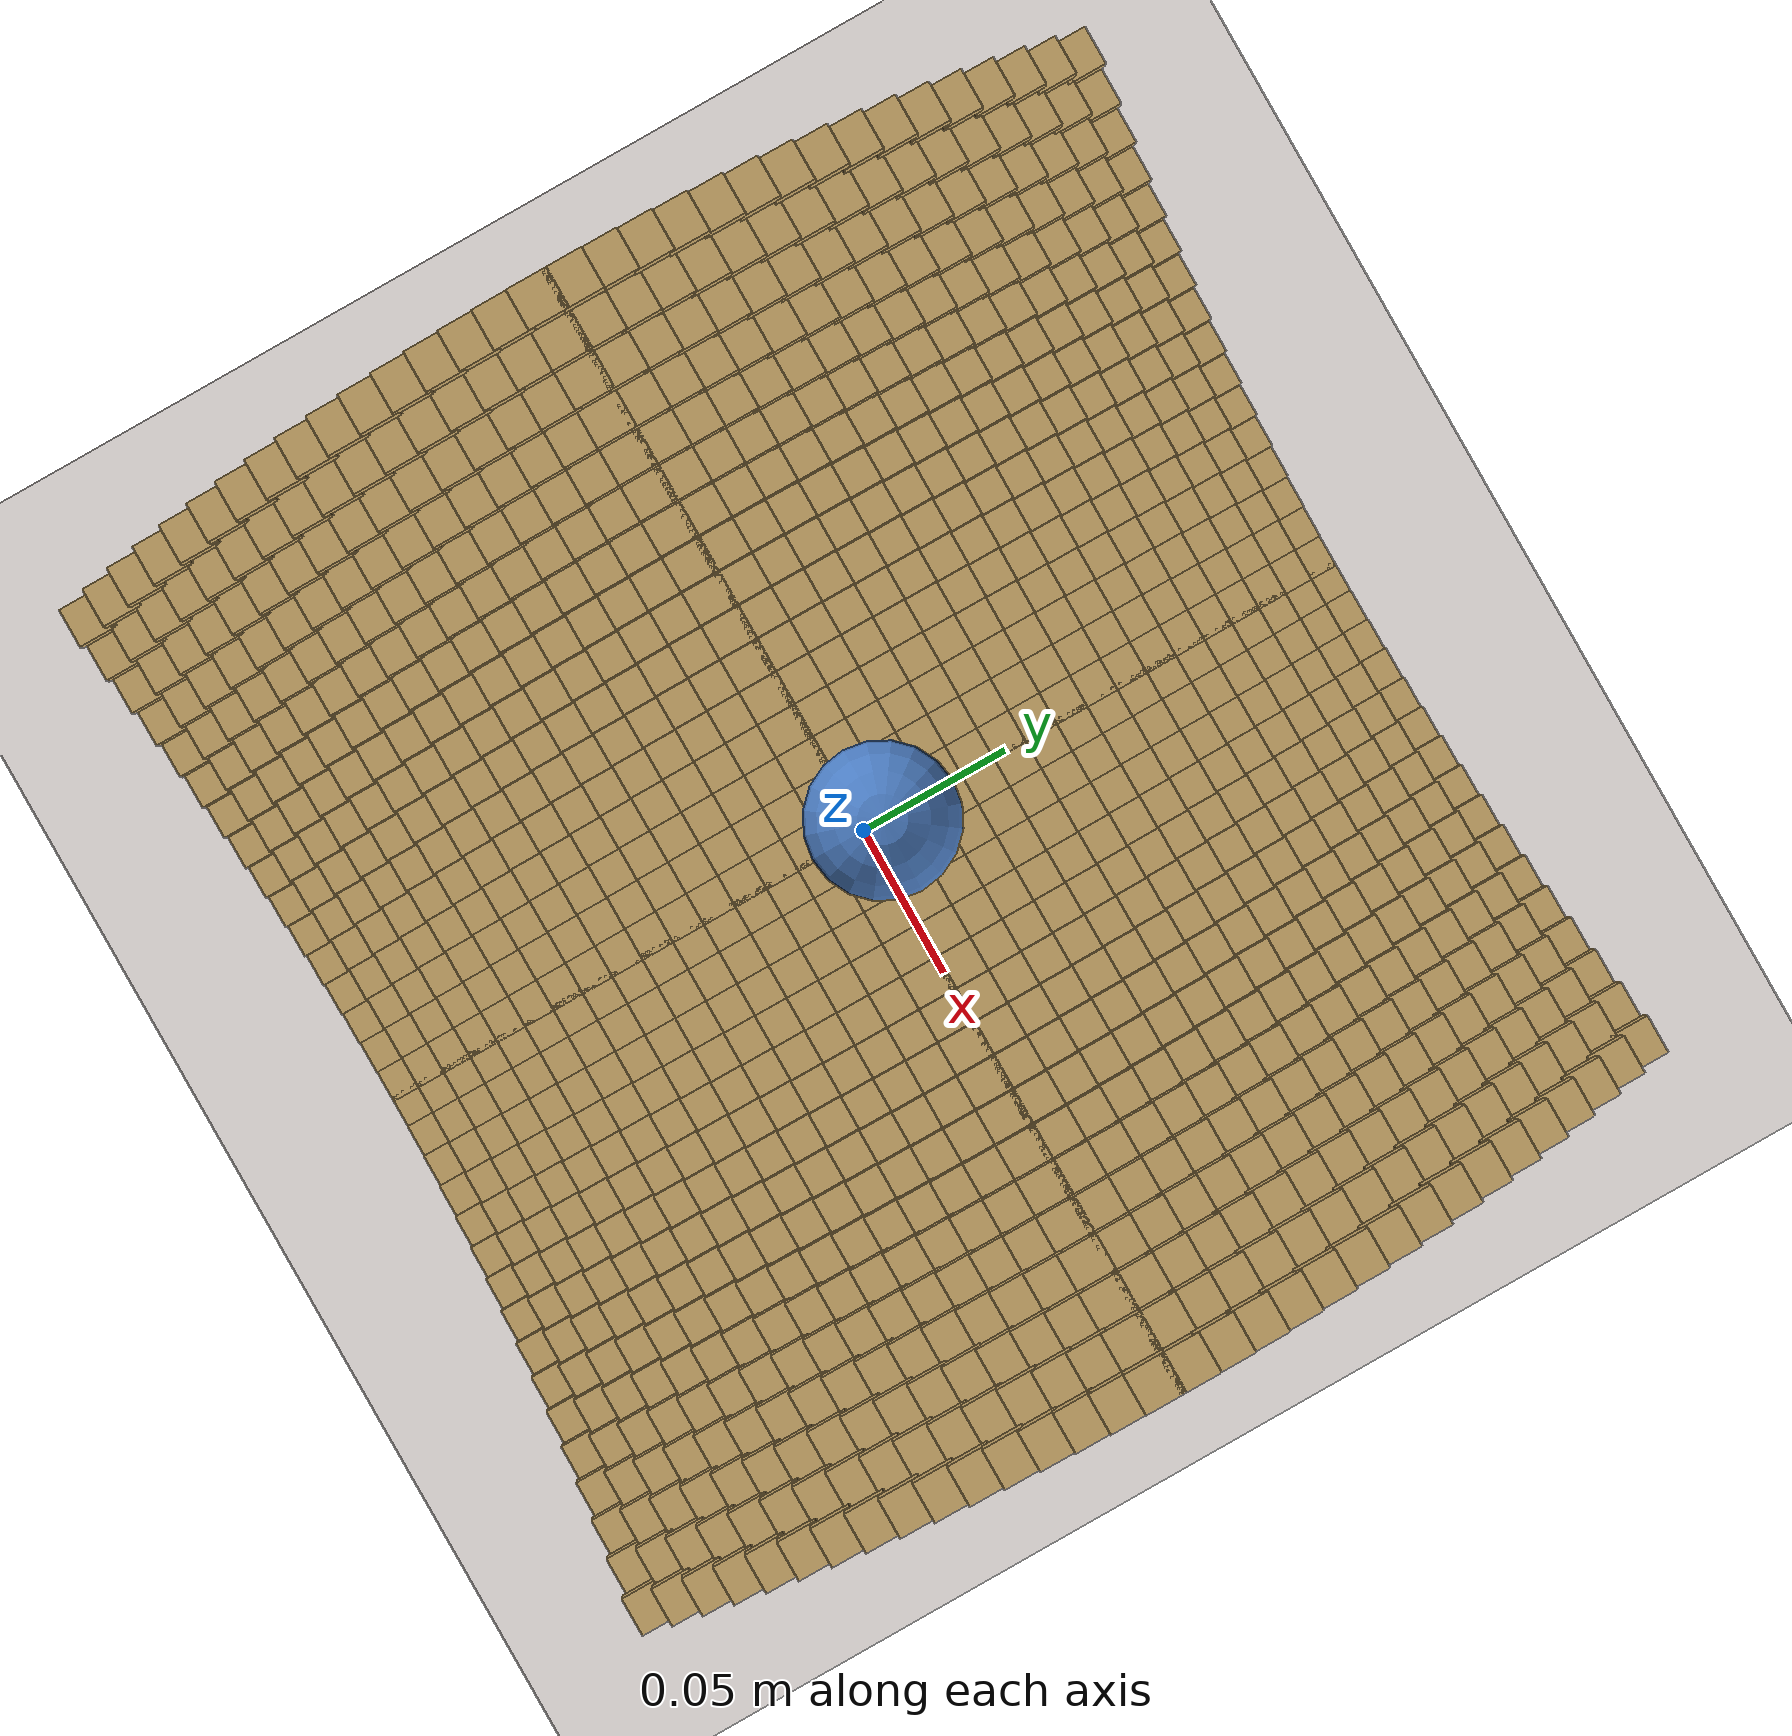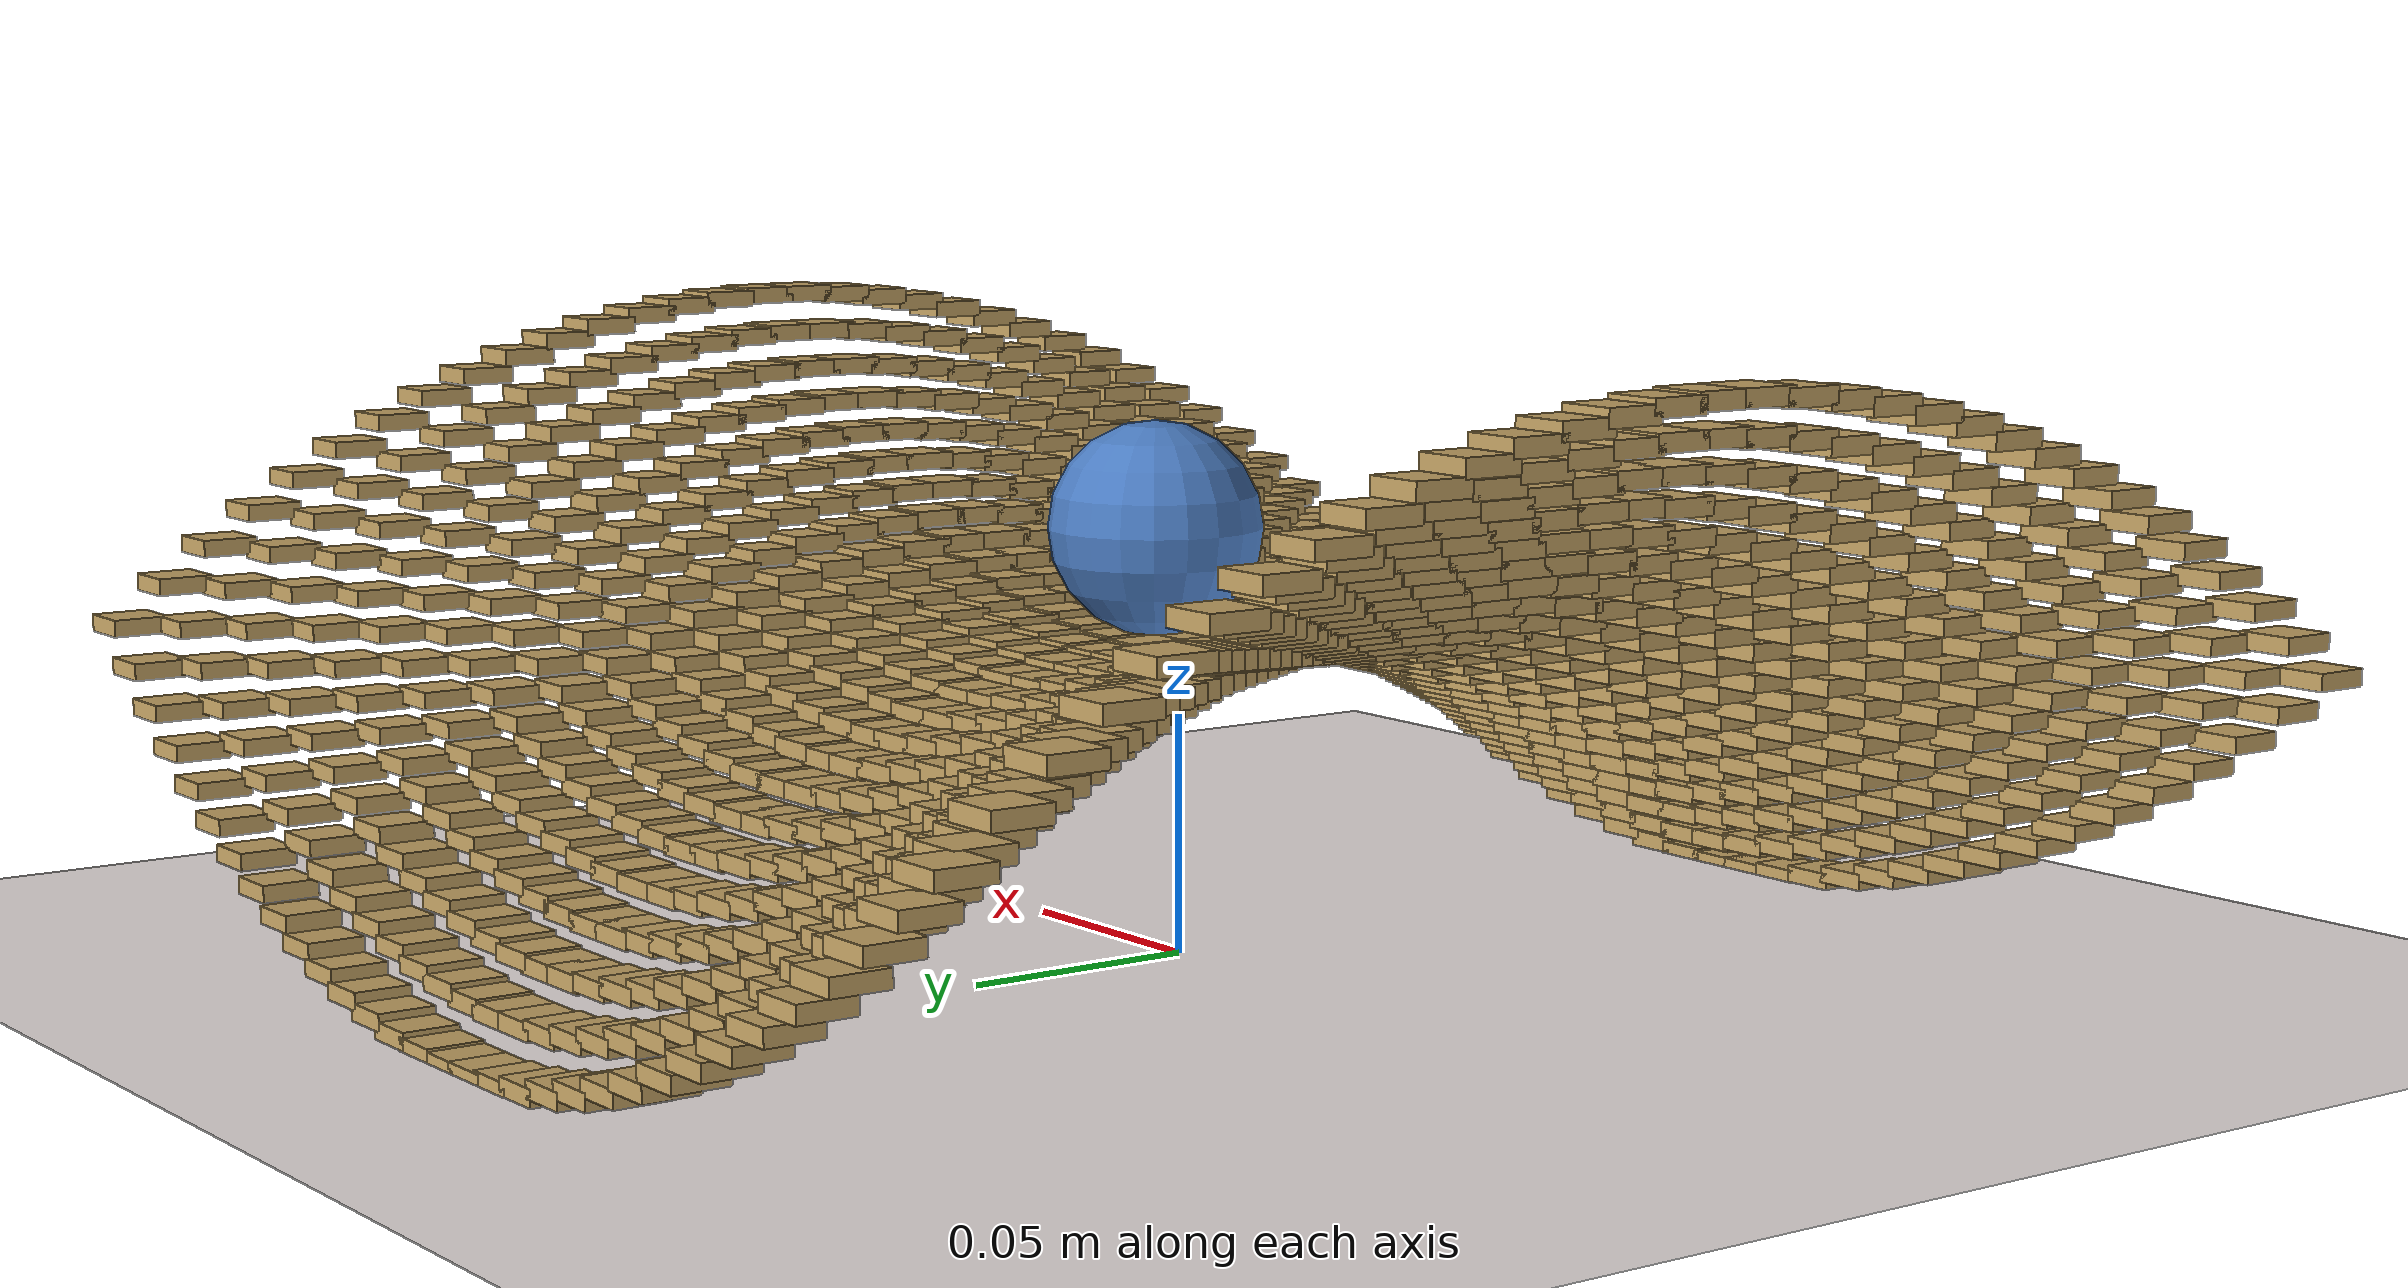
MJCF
<mujoco model="ball_on_saddle">
  <!-- Saddle z = 2.5*(x² − y²) + 0.062; ball rolls along +y (unstable axis).
       Render 1.0 s with --init-qvel "0,0.02,0,0,0,0" -->
  <compiler angle="radian" coordinate="local" autolimits="true"/>
  <option timestep="0.0005" gravity="0 0 -9.81" integrator="implicitfast"
          impratio="5" cone="elliptic"/>

  <visual>
    <headlight diffuse="0 0 0" ambient="0.50 0.48 0.55" specular="0 0 0"/>
    <rgba haze="0.94 0.91 0.90 1"/>
    <global azimuth="120" elevation="-15" offwidth="1920" offheight="1080" fovy="38"/>
    <quality shadowsize="8192" offsamples="8"/>
    <map shadowclip="6" shadowscale="0.7"/>
  </visual>

  <asset>
    <texture type="skybox" builtin="flat"
             rgb1="0.74 0.68 0.86" rgb2="0.74 0.68 0.86"
             width="512" height="512" mark="none" markrgb="0 0 0"/>
    <material name="floor_mat" rgba="0.94 0.91 0.90 1" specular="0" shininess="0"/>
    <material name="saddle_mat" rgba="0.78 0.65 0.40 1" specular="0.12" shininess="0.15"/>
    <material name="ball_blue" rgba="0.30 0.50 0.78 1" specular="0.55" shininess="0.65"/>
  </asset>

  <default>
    <geom friction="0.07 0.003 0.0001" solref="0.003 1" solimp="0.96 0.99 0.001"/>
  </default>

  <worldbody>
    <light pos="0 0 12" dir="-0.30 0.55 -1" directional="true" castshadow="true"
           diffuse="0.85 0.82 0.78" specular="0.15 0.15 0.15"/>
    <light pos="0 0 8" dir="0.40 -0.30 -1" directional="true" castshadow="false"
           diffuse="0.28 0.28 0.34" specular="0 0 0"/>

    <geom name="floor" type="plane" size="40 40 0.1" material="floor_mat"
          contype="0" conaffinity="0"/>

    <geom type="box" pos="-0.1600 -0.1600 0.06380" size="0.00599 0.00599 0.0018" material="saddle_mat"/>
    <geom type="box" pos="-0.1600 -0.1497 0.07179" size="0.00599 0.00599 0.0018" material="saddle_mat"/>
    <geom type="box" pos="-0.1600 -0.1394 0.07925" size="0.00599 0.00599 0.0018" material="saddle_mat"/>
    <geom type="box" pos="-0.1600 -0.1290 0.08618" size="0.00599 0.00599 0.0018" material="saddle_mat"/>
    <geom type="box" pos="-0.1600 -0.1187 0.09257" size="0.00599 0.00599 0.0018" material="saddle_mat"/>
    <geom type="box" pos="-0.1600 -0.1084 0.09843" size="0.00599 0.00599 0.0018" material="saddle_mat"/>
    <geom type="box" pos="-0.1600 -0.0981 0.10376" size="0.00599 0.00599 0.0018" material="saddle_mat"/>
    <geom type="box" pos="-0.1600 -0.0877 0.10855" size="0.00599 0.00599 0.0018" material="saddle_mat"/>
    <geom type="box" pos="-0.1600 -0.0774 0.11282" size="0.00599 0.00599 0.0018" material="saddle_mat"/>
    <geom type="box" pos="-0.1600 -0.0671 0.11655" size="0.00599 0.00599 0.0018" material="saddle_mat"/>
    <geom type="box" pos="-0.1600 -0.0568 0.11974" size="0.00599 0.00599 0.0018" material="saddle_mat"/>
    <geom type="box" pos="-0.1600 -0.0465 0.12241" size="0.00599 0.00599 0.0018" material="saddle_mat"/>
    <geom type="box" pos="-0.1600 -0.0361 0.12454" size="0.00599 0.00599 0.0018" material="saddle_mat"/>
    <geom type="box" pos="-0.1600 -0.0258 0.12614" size="0.00599 0.00599 0.0018" material="saddle_mat"/>
    <geom type="box" pos="-0.1600 -0.0155 0.12720" size="0.00599 0.00599 0.0018" material="saddle_mat"/>
    <geom type="box" pos="-0.1600 -0.0052 0.12773" size="0.00599 0.00599 0.0018" material="saddle_mat"/>
    <geom type="box" pos="-0.1600 0.0052 0.12773" size="0.00599 0.00599 0.0018" material="saddle_mat"/>
    <geom type="box" pos="-0.1600 0.0155 0.12720" size="0.00599 0.00599 0.0018" material="saddle_mat"/>
    <geom type="box" pos="-0.1600 0.0258 0.12614" size="0.00599 0.00599 0.0018" material="saddle_mat"/>
    <geom type="box" pos="-0.1600 0.0361 0.12454" size="0.00599 0.00599 0.0018" material="saddle_mat"/>
    <geom type="box" pos="-0.1600 0.0465 0.12241" size="0.00599 0.00599 0.0018" material="saddle_mat"/>
    <geom type="box" pos="-0.1600 0.0568 0.11974" size="0.00599 0.00599 0.0018" material="saddle_mat"/>
    <geom type="box" pos="-0.1600 0.0671 0.11655" size="0.00599 0.00599 0.0018" material="saddle_mat"/>
    <geom type="box" pos="-0.1600 0.0774 0.11282" size="0.00599 0.00599 0.0018" material="saddle_mat"/>
    <geom type="box" pos="-0.1600 0.0877 0.10855" size="0.00599 0.00599 0.0018" material="saddle_mat"/>
    <geom type="box" pos="-0.1600 0.0981 0.10376" size="0.00599 0.00599 0.0018" material="saddle_mat"/>
    <geom type="box" pos="-0.1600 0.1084 0.09843" size="0.00599 0.00599 0.0018" material="saddle_mat"/>
    <geom type="box" pos="-0.1600 0.1187 0.09257" size="0.00599 0.00599 0.0018" material="saddle_mat"/>
    <geom type="box" pos="-0.1600 0.1290 0.08618" size="0.00599 0.00599 0.0018" material="saddle_mat"/>
    <geom type="box" pos="-0.1600 0.1394 0.07925" size="0.00599 0.00599 0.0018" material="saddle_mat"/>
    <geom type="box" pos="-0.1600 0.1497 0.07179" size="0.00599 0.00599 0.0018" material="saddle_mat"/>
    <geom type="box" pos="-0.1600 0.1600 0.06380" size="0.00599 0.00599 0.0018" material="saddle_mat"/>
    <geom type="box" pos="-0.1497 -0.1600 0.05581" size="0.00599 0.00599 0.0018" material="saddle_mat"/>
    <geom type="box" pos="-0.1497 -0.1497 0.06380" size="0.00599 0.00599 0.0018" material="saddle_mat"/>
    <geom type="box" pos="-0.1497 -0.1394 0.07126" size="0.00599 0.00599 0.0018" material="saddle_mat"/>
    <geom type="box" pos="-0.1497 -0.1290 0.07819" size="0.00599 0.00599 0.0018" material="saddle_mat"/>
    <geom type="box" pos="-0.1497 -0.1187 0.08458" size="0.00599 0.00599 0.0018" material="saddle_mat"/>
    <geom type="box" pos="-0.1497 -0.1084 0.09044" size="0.00599 0.00599 0.0018" material="saddle_mat"/>
    <geom type="box" pos="-0.1497 -0.0981 0.09577" size="0.00599 0.00599 0.0018" material="saddle_mat"/>
    <geom type="box" pos="-0.1497 -0.0877 0.10056" size="0.00599 0.00599 0.0018" material="saddle_mat"/>
    <geom type="box" pos="-0.1497 -0.0774 0.10482" size="0.00599 0.00599 0.0018" material="saddle_mat"/>
    <geom type="box" pos="-0.1497 -0.0671 0.10855" size="0.00599 0.00599 0.0018" material="saddle_mat"/>
    <geom type="box" pos="-0.1497 -0.0568 0.11175" size="0.00599 0.00599 0.0018" material="saddle_mat"/>
    <geom type="box" pos="-0.1497 -0.0465 0.11441" size="0.00599 0.00599 0.0018" material="saddle_mat"/>
    <geom type="box" pos="-0.1497 -0.0361 0.11655" size="0.00599 0.00599 0.0018" material="saddle_mat"/>
    <geom type="box" pos="-0.1497 -0.0258 0.11814" size="0.00599 0.00599 0.0018" material="saddle_mat"/>
    <geom type="box" pos="-0.1497 -0.0155 0.11921" size="0.00599 0.00599 0.0018" material="saddle_mat"/>
    <geom type="box" pos="-0.1497 -0.0052 0.11974" size="0.00599 0.00599 0.0018" material="saddle_mat"/>
    <geom type="box" pos="-0.1497 0.0052 0.11974" size="0.00599 0.00599 0.0018" material="saddle_mat"/>
    <geom type="box" pos="-0.1497 0.0155 0.11921" size="0.00599 0.00599 0.0018" material="saddle_mat"/>
    <geom type="box" pos="-0.1497 0.0258 0.11814" size="0.00599 0.00599 0.0018" material="saddle_mat"/>
    <geom type="box" pos="-0.1497 0.0361 0.11655" size="0.00599 0.00599 0.0018" material="saddle_mat"/>
    <geom type="box" pos="-0.1497 0.0465 0.11441" size="0.00599 0.00599 0.0018" material="saddle_mat"/>
    <geom type="box" pos="-0.1497 0.0568 0.11175" size="0.00599 0.00599 0.0018" material="saddle_mat"/>
    <geom type="box" pos="-0.1497 0.0671 0.10855" size="0.00599 0.00599 0.0018" material="saddle_mat"/>
    <geom type="box" pos="-0.1497 0.0774 0.10482" size="0.00599 0.00599 0.0018" material="saddle_mat"/>
    <geom type="box" pos="-0.1497 0.0877 0.10056" size="0.00599 0.00599 0.0018" material="saddle_mat"/>
    <geom type="box" pos="-0.1497 0.0981 0.09577" size="0.00599 0.00599 0.0018" material="saddle_mat"/>
    <geom type="box" pos="-0.1497 0.1084 0.09044" size="0.00599 0.00599 0.0018" material="saddle_mat"/>
    <geom type="box" pos="-0.1497 0.1187 0.08458" size="0.00599 0.00599 0.0018" material="saddle_mat"/>
    <geom type="box" pos="-0.1497 0.1290 0.07819" size="0.00599 0.00599 0.0018" material="saddle_mat"/>
    <geom type="box" pos="-0.1497 0.1394 0.07126" size="0.00599 0.00599 0.0018" material="saddle_mat"/>
    <geom type="box" pos="-0.1497 0.1497 0.06380" size="0.00599 0.00599 0.0018" material="saddle_mat"/>
    <geom type="box" pos="-0.1497 0.1600 0.05581" size="0.00599 0.00599 0.0018" material="saddle_mat"/>
    <geom type="box" pos="-0.1394 -0.1600 0.04835" size="0.00599 0.00599 0.0018" material="saddle_mat"/>
    <geom type="box" pos="-0.1394 -0.1497 0.05634" size="0.00599 0.00599 0.0018" material="saddle_mat"/>
    <geom type="box" pos="-0.1394 -0.1394 0.06380" size="0.00599 0.00599 0.0018" material="saddle_mat"/>
    <geom type="box" pos="-0.1394 -0.1290 0.07073" size="0.00599 0.00599 0.0018" material="saddle_mat"/>
    <geom type="box" pos="-0.1394 -0.1187 0.07712" size="0.00599 0.00599 0.0018" material="saddle_mat"/>
    <geom type="box" pos="-0.1394 -0.1084 0.08298" size="0.00599 0.00599 0.0018" material="saddle_mat"/>
    <geom type="box" pos="-0.1394 -0.0981 0.08831" size="0.00599 0.00599 0.0018" material="saddle_mat"/>
    <geom type="box" pos="-0.1394 -0.0877 0.09310" size="0.00599 0.00599 0.0018" material="saddle_mat"/>
    <geom type="box" pos="-0.1394 -0.0774 0.09737" size="0.00599 0.00599 0.0018" material="saddle_mat"/>
    <geom type="box" pos="-0.1394 -0.0671 0.10109" size="0.00599 0.00599 0.0018" material="saddle_mat"/>
    <geom type="box" pos="-0.1394 -0.0568 0.10429" size="0.00599 0.00599 0.0018" material="saddle_mat"/>
    <geom type="box" pos="-0.1394 -0.0465 0.10696" size="0.00599 0.00599 0.0018" material="saddle_mat"/>
    <geom type="box" pos="-0.1394 -0.0361 0.10909" size="0.00599 0.00599 0.0018" material="saddle_mat"/>
    <geom type="box" pos="-0.1394 -0.0258 0.11068" size="0.00599 0.00599 0.0018" material="saddle_mat"/>
    <geom type="box" pos="-0.1394 -0.0155 0.11175" size="0.00599 0.00599 0.0018" material="saddle_mat"/>
    <geom type="box" pos="-0.1394 -0.0052 0.11228" size="0.00599 0.00599 0.0018" material="saddle_mat"/>
    <geom type="box" pos="-0.1394 0.0052 0.11228" size="0.00599 0.00599 0.0018" material="saddle_mat"/>
    <geom type="box" pos="-0.1394 0.0155 0.11175" size="0.00599 0.00599 0.0018" material="saddle_mat"/>
    <geom type="box" pos="-0.1394 0.0258 0.11068" size="0.00599 0.00599 0.0018" material="saddle_mat"/>
    <geom type="box" pos="-0.1394 0.0361 0.10909" size="0.00599 0.00599 0.0018" material="saddle_mat"/>
    <geom type="box" pos="-0.1394 0.0465 0.10696" size="0.00599 0.00599 0.0018" material="saddle_mat"/>
    <geom type="box" pos="-0.1394 0.0568 0.10429" size="0.00599 0.00599 0.0018" material="saddle_mat"/>
    <geom type="box" pos="-0.1394 0.0671 0.10109" size="0.00599 0.00599 0.0018" material="saddle_mat"/>
    <geom type="box" pos="-0.1394 0.0774 0.09737" size="0.00599 0.00599 0.0018" material="saddle_mat"/>
    <geom type="box" pos="-0.1394 0.0877 0.09310" size="0.00599 0.00599 0.0018" material="saddle_mat"/>
    <geom type="box" pos="-0.1394 0.0981 0.08831" size="0.00599 0.00599 0.0018" material="saddle_mat"/>
    <geom type="box" pos="-0.1394 0.1084 0.08298" size="0.00599 0.00599 0.0018" material="saddle_mat"/>
    <geom type="box" pos="-0.1394 0.1187 0.07712" size="0.00599 0.00599 0.0018" material="saddle_mat"/>
    <geom type="box" pos="-0.1394 0.1290 0.07073" size="0.00599 0.00599 0.0018" material="saddle_mat"/>
    <geom type="box" pos="-0.1394 0.1394 0.06380" size="0.00599 0.00599 0.0018" material="saddle_mat"/>
    <geom type="box" pos="-0.1394 0.1497 0.05634" size="0.00599 0.00599 0.0018" material="saddle_mat"/>
    <geom type="box" pos="-0.1394 0.1600 0.04835" size="0.00599 0.00599 0.0018" material="saddle_mat"/>
    <geom type="box" pos="-0.1290 -0.1600 0.04142" size="0.00599 0.00599 0.0018" material="saddle_mat"/>
    <geom type="box" pos="-0.1290 -0.1497 0.04941" size="0.00599 0.00599 0.0018" material="saddle_mat"/>
    <geom type="box" pos="-0.1290 -0.1394 0.05687" size="0.00599 0.00599 0.0018" material="saddle_mat"/>
    <geom type="box" pos="-0.1290 -0.1290 0.06380" size="0.00599 0.00599 0.0018" material="saddle_mat"/>
    <geom type="box" pos="-0.1290 -0.1187 0.07019" size="0.00599 0.00599 0.0018" material="saddle_mat"/>
    <geom type="box" pos="-0.1290 -0.1084 0.07605" size="0.00599 0.00599 0.0018" material="saddle_mat"/>
    <geom type="box" pos="-0.1290 -0.0981 0.08138" size="0.00599 0.00599 0.0018" material="saddle_mat"/>
    <geom type="box" pos="-0.1290 -0.0877 0.08618" size="0.00599 0.00599 0.0018" material="saddle_mat"/>
    <geom type="box" pos="-0.1290 -0.0774 0.09044" size="0.00599 0.00599 0.0018" material="saddle_mat"/>
    <geom type="box" pos="-0.1290 -0.0671 0.09417" size="0.00599 0.00599 0.0018" material="saddle_mat"/>
    <geom type="box" pos="-0.1290 -0.0568 0.09737" size="0.00599 0.00599 0.0018" material="saddle_mat"/>
    <geom type="box" pos="-0.1290 -0.0465 0.10003" size="0.00599 0.00599 0.0018" material="saddle_mat"/>
    <geom type="box" pos="-0.1290 -0.0361 0.10216" size="0.00599 0.00599 0.0018" material="saddle_mat"/>
    <geom type="box" pos="-0.1290 -0.0258 0.10376" size="0.00599 0.00599 0.0018" material="saddle_mat"/>
    <geom type="box" pos="-0.1290 -0.0155 0.10482" size="0.00599 0.00599 0.0018" material="saddle_mat"/>
    <geom type="box" pos="-0.1290 -0.0052 0.10536" size="0.00599 0.00599 0.0018" material="saddle_mat"/>
    <geom type="box" pos="-0.1290 0.0052 0.10536" size="0.00599 0.00599 0.0018" material="saddle_mat"/>
    <geom type="box" pos="-0.1290 0.0155 0.10482" size="0.00599 0.00599 0.0018" material="saddle_mat"/>
    <geom type="box" pos="-0.1290 0.0258 0.10376" size="0.00599 0.00599 0.0018" material="saddle_mat"/>
    <geom type="box" pos="-0.1290 0.0361 0.10216" size="0.00599 0.00599 0.0018" material="saddle_mat"/>
    <geom type="box" pos="-0.1290 0.0465 0.10003" size="0.00599 0.00599 0.0018" material="saddle_mat"/>
    <geom type="box" pos="-0.1290 0.0568 0.09737" size="0.00599 0.00599 0.0018" material="saddle_mat"/>
    <geom type="box" pos="-0.1290 0.0671 0.09417" size="0.00599 0.00599 0.0018" material="saddle_mat"/>
    <geom type="box" pos="-0.1290 0.0774 0.09044" size="0.00599 0.00599 0.0018" material="saddle_mat"/>
    <geom type="box" pos="-0.1290 0.0877 0.08618" size="0.00599 0.00599 0.0018" material="saddle_mat"/>
    <geom type="box" pos="-0.1290 0.0981 0.08138" size="0.00599 0.00599 0.0018" material="saddle_mat"/>
    <geom type="box" pos="-0.1290 0.1084 0.07605" size="0.00599 0.00599 0.0018" material="saddle_mat"/>
    <geom type="box" pos="-0.1290 0.1187 0.07019" size="0.00599 0.00599 0.0018" material="saddle_mat"/>
    <geom type="box" pos="-0.1290 0.1290 0.06380" size="0.00599 0.00599 0.0018" material="saddle_mat"/>
    <geom type="box" pos="-0.1290 0.1394 0.05687" size="0.00599 0.00599 0.0018" material="saddle_mat"/>
    <geom type="box" pos="-0.1290 0.1497 0.04941" size="0.00599 0.00599 0.0018" material="saddle_mat"/>
    <geom type="box" pos="-0.1290 0.1600 0.04142" size="0.00599 0.00599 0.0018" material="saddle_mat"/>
    <geom type="box" pos="-0.1187 -0.1600 0.03503" size="0.00599 0.00599 0.0018" material="saddle_mat"/>
    <geom type="box" pos="-0.1187 -0.1497 0.04302" size="0.00599 0.00599 0.0018" material="saddle_mat"/>
    <geom type="box" pos="-0.1187 -0.1394 0.05048" size="0.00599 0.00599 0.0018" material="saddle_mat"/>
    <geom type="box" pos="-0.1187 -0.1290 0.05741" size="0.00599 0.00599 0.0018" material="saddle_mat"/>
    <geom type="box" pos="-0.1187 -0.1187 0.06380" size="0.00599 0.00599 0.0018" material="saddle_mat"/>
    <geom type="box" pos="-0.1187 -0.1084 0.06966" size="0.00599 0.00599 0.0018" material="saddle_mat"/>
    <geom type="box" pos="-0.1187 -0.0981 0.07499" size="0.00599 0.00599 0.0018" material="saddle_mat"/>
    <geom type="box" pos="-0.1187 -0.0877 0.07978" size="0.00599 0.00599 0.0018" material="saddle_mat"/>
    <geom type="box" pos="-0.1187 -0.0774 0.08405" size="0.00599 0.00599 0.0018" material="saddle_mat"/>
    <geom type="box" pos="-0.1187 -0.0671 0.08778" size="0.00599 0.00599 0.0018" material="saddle_mat"/>
    <geom type="box" pos="-0.1187 -0.0568 0.09097" size="0.00599 0.00599 0.0018" material="saddle_mat"/>
    <geom type="box" pos="-0.1187 -0.0465 0.09364" size="0.00599 0.00599 0.0018" material="saddle_mat"/>
    <geom type="box" pos="-0.1187 -0.0361 0.09577" size="0.00599 0.00599 0.0018" material="saddle_mat"/>
    <geom type="box" pos="-0.1187 -0.0258 0.09737" size="0.00599 0.00599 0.0018" material="saddle_mat"/>
    <geom type="box" pos="-0.1187 -0.0155 0.09843" size="0.00599 0.00599 0.0018" material="saddle_mat"/>
    <geom type="box" pos="-0.1187 -0.0052 0.09896" size="0.00599 0.00599 0.0018" material="saddle_mat"/>
    <geom type="box" pos="-0.1187 0.0052 0.09896" size="0.00599 0.00599 0.0018" material="saddle_mat"/>
    <geom type="box" pos="-0.1187 0.0155 0.09843" size="0.00599 0.00599 0.0018" material="saddle_mat"/>
    <geom type="box" pos="-0.1187 0.0258 0.09737" size="0.00599 0.00599 0.0018" material="saddle_mat"/>
    <geom type="box" pos="-0.1187 0.0361 0.09577" size="0.00599 0.00599 0.0018" material="saddle_mat"/>
    <geom type="box" pos="-0.1187 0.0465 0.09364" size="0.00599 0.00599 0.0018" material="saddle_mat"/>
    <geom type="box" pos="-0.1187 0.0568 0.09097" size="0.00599 0.00599 0.0018" material="saddle_mat"/>
    <geom type="box" pos="-0.1187 0.0671 0.08778" size="0.00599 0.00599 0.0018" material="saddle_mat"/>
    <geom type="box" pos="-0.1187 0.0774 0.08405" size="0.00599 0.00599 0.0018" material="saddle_mat"/>
    <geom type="box" pos="-0.1187 0.0877 0.07978" size="0.00599 0.00599 0.0018" material="saddle_mat"/>
    <geom type="box" pos="-0.1187 0.0981 0.07499" size="0.00599 0.00599 0.0018" material="saddle_mat"/>
    <geom type="box" pos="-0.1187 0.1084 0.06966" size="0.00599 0.00599 0.0018" material="saddle_mat"/>
    <geom type="box" pos="-0.1187 0.1187 0.06380" size="0.00599 0.00599 0.0018" material="saddle_mat"/>
    <geom type="box" pos="-0.1187 0.1290 0.05741" size="0.00599 0.00599 0.0018" material="saddle_mat"/>
    <geom type="box" pos="-0.1187 0.1394 0.05048" size="0.00599 0.00599 0.0018" material="saddle_mat"/>
    <geom type="box" pos="-0.1187 0.1497 0.04302" size="0.00599 0.00599 0.0018" material="saddle_mat"/>
    <geom type="box" pos="-0.1187 0.1600 0.03503" size="0.00599 0.00599 0.0018" material="saddle_mat"/>
    <geom type="box" pos="-0.1084 -0.1600 0.02917" size="0.00599 0.00599 0.0018" material="saddle_mat"/>
    <geom type="box" pos="-0.1084 -0.1497 0.03716" size="0.00599 0.00599 0.0018" material="saddle_mat"/>
    <geom type="box" pos="-0.1084 -0.1394 0.04462" size="0.00599 0.00599 0.0018" material="saddle_mat"/>
    <geom type="box" pos="-0.1084 -0.1290 0.05155" size="0.00599 0.00599 0.0018" material="saddle_mat"/>
    <geom type="box" pos="-0.1084 -0.1187 0.05794" size="0.00599 0.00599 0.0018" material="saddle_mat"/>
    <geom type="box" pos="-0.1084 -0.1084 0.06380" size="0.00599 0.00599 0.0018" material="saddle_mat"/>
    <geom type="box" pos="-0.1084 -0.0981 0.06913" size="0.00599 0.00599 0.0018" material="saddle_mat"/>
    <geom type="box" pos="-0.1084 -0.0877 0.07392" size="0.00599 0.00599 0.0018" material="saddle_mat"/>
    <geom type="box" pos="-0.1084 -0.0774 0.07819" size="0.00599 0.00599 0.0018" material="saddle_mat"/>
    <geom type="box" pos="-0.1084 -0.0671 0.08191" size="0.00599 0.00599 0.0018" material="saddle_mat"/>
    <geom type="box" pos="-0.1084 -0.0568 0.08511" size="0.00599 0.00599 0.0018" material="saddle_mat"/>
    <geom type="box" pos="-0.1084 -0.0465 0.08778" size="0.00599 0.00599 0.0018" material="saddle_mat"/>
    <geom type="box" pos="-0.1084 -0.0361 0.08991" size="0.00599 0.00599 0.0018" material="saddle_mat"/>
    <geom type="box" pos="-0.1084 -0.0258 0.09150" size="0.00599 0.00599 0.0018" material="saddle_mat"/>
    <geom type="box" pos="-0.1084 -0.0155 0.09257" size="0.00599 0.00599 0.0018" material="saddle_mat"/>
    <geom type="box" pos="-0.1084 -0.0052 0.09310" size="0.00599 0.00599 0.0018" material="saddle_mat"/>
    <geom type="box" pos="-0.1084 0.0052 0.09310" size="0.00599 0.00599 0.0018" material="saddle_mat"/>
    <geom type="box" pos="-0.1084 0.0155 0.09257" size="0.00599 0.00599 0.0018" material="saddle_mat"/>
    <geom type="box" pos="-0.1084 0.0258 0.09150" size="0.00599 0.00599 0.0018" material="saddle_mat"/>
    <geom type="box" pos="-0.1084 0.0361 0.08991" size="0.00599 0.00599 0.0018" material="saddle_mat"/>
    <geom type="box" pos="-0.1084 0.0465 0.08778" size="0.00599 0.00599 0.0018" material="saddle_mat"/>
    <geom type="box" pos="-0.1084 0.0568 0.08511" size="0.00599 0.00599 0.0018" material="saddle_mat"/>
    <geom type="box" pos="-0.1084 0.0671 0.08191" size="0.00599 0.00599 0.0018" material="saddle_mat"/>
    <geom type="box" pos="-0.1084 0.0774 0.07819" size="0.00599 0.00599 0.0018" material="saddle_mat"/>
    <geom type="box" pos="-0.1084 0.0877 0.07392" size="0.00599 0.00599 0.0018" material="saddle_mat"/>
    <geom type="box" pos="-0.1084 0.0981 0.06913" size="0.00599 0.00599 0.0018" material="saddle_mat"/>
    <geom type="box" pos="-0.1084 0.1084 0.06380" size="0.00599 0.00599 0.0018" material="saddle_mat"/>
    <geom type="box" pos="-0.1084 0.1187 0.05794" size="0.00599 0.00599 0.0018" material="saddle_mat"/>
    <geom type="box" pos="-0.1084 0.1290 0.05155" size="0.00599 0.00599 0.0018" material="saddle_mat"/>
    <geom type="box" pos="-0.1084 0.1394 0.04462" size="0.00599 0.00599 0.0018" material="saddle_mat"/>
    <geom type="box" pos="-0.1084 0.1497 0.03716" size="0.00599 0.00599 0.0018" material="saddle_mat"/>
    <geom type="box" pos="-0.1084 0.1600 0.02917" size="0.00599 0.00599 0.0018" material="saddle_mat"/>
    <geom type="box" pos="-0.0981 -0.1600 0.02384" size="0.00599 0.00599 0.0018" material="saddle_mat"/>
    <geom type="box" pos="-0.0981 -0.1497 0.03183" size="0.00599 0.00599 0.0018" material="saddle_mat"/>
    <geom type="box" pos="-0.0981 -0.1394 0.03929" size="0.00599 0.00599 0.0018" material="saddle_mat"/>
    <geom type="box" pos="-0.0981 -0.1290 0.04622" size="0.00599 0.00599 0.0018" material="saddle_mat"/>
    <geom type="box" pos="-0.0981 -0.1187 0.05261" size="0.00599 0.00599 0.0018" material="saddle_mat"/>
    <geom type="box" pos="-0.0981 -0.1084 0.05847" size="0.00599 0.00599 0.0018" material="saddle_mat"/>
    <geom type="box" pos="-0.0981 -0.0981 0.06380" size="0.00599 0.00599 0.0018" material="saddle_mat"/>
    <geom type="box" pos="-0.0981 -0.0877 0.06860" size="0.00599 0.00599 0.0018" material="saddle_mat"/>
    <geom type="box" pos="-0.0981 -0.0774 0.07286" size="0.00599 0.00599 0.0018" material="saddle_mat"/>
    <geom type="box" pos="-0.0981 -0.0671 0.07659" size="0.00599 0.00599 0.0018" material="saddle_mat"/>
    <geom type="box" pos="-0.0981 -0.0568 0.07978" size="0.00599 0.00599 0.0018" material="saddle_mat"/>
    <geom type="box" pos="-0.0981 -0.0465 0.08245" size="0.00599 0.00599 0.0018" material="saddle_mat"/>
    <geom type="box" pos="-0.0981 -0.0361 0.08458" size="0.00599 0.00599 0.0018" material="saddle_mat"/>
    <geom type="box" pos="-0.0981 -0.0258 0.08618" size="0.00599 0.00599 0.0018" material="saddle_mat"/>
    <geom type="box" pos="-0.0981 -0.0155 0.08724" size="0.00599 0.00599 0.0018" material="saddle_mat"/>
    <geom type="box" pos="-0.0981 -0.0052 0.08778" size="0.00599 0.00599 0.0018" material="saddle_mat"/>
    <geom type="box" pos="-0.0981 0.0052 0.08778" size="0.00599 0.00599 0.0018" material="saddle_mat"/>
    <geom type="box" pos="-0.0981 0.0155 0.08724" size="0.00599 0.00599 0.0018" material="saddle_mat"/>
    <geom type="box" pos="-0.0981 0.0258 0.08618" size="0.00599 0.00599 0.0018" material="saddle_mat"/>
    <geom type="box" pos="-0.0981 0.0361 0.08458" size="0.00599 0.00599 0.0018" material="saddle_mat"/>
    <geom type="box" pos="-0.0981 0.0465 0.08245" size="0.00599 0.00599 0.0018" material="saddle_mat"/>
    <geom type="box" pos="-0.0981 0.0568 0.07978" size="0.00599 0.00599 0.0018" material="saddle_mat"/>
    <geom type="box" pos="-0.0981 0.0671 0.07659" size="0.00599 0.00599 0.0018" material="saddle_mat"/>
    <geom type="box" pos="-0.0981 0.0774 0.07286" size="0.00599 0.00599 0.0018" material="saddle_mat"/>
    <geom type="box" pos="-0.0981 0.0877 0.06860" size="0.00599 0.00599 0.0018" material="saddle_mat"/>
    <geom type="box" pos="-0.0981 0.0981 0.06380" size="0.00599 0.00599 0.0018" material="saddle_mat"/>
    <geom type="box" pos="-0.0981 0.1084 0.05847" size="0.00599 0.00599 0.0018" material="saddle_mat"/>
    <geom type="box" pos="-0.0981 0.1187 0.05261" size="0.00599 0.00599 0.0018" material="saddle_mat"/>
    <geom type="box" pos="-0.0981 0.1290 0.04622" size="0.00599 0.00599 0.0018" material="saddle_mat"/>
    <geom type="box" pos="-0.0981 0.1394 0.03929" size="0.00599 0.00599 0.0018" material="saddle_mat"/>
    <geom type="box" pos="-0.0981 0.1497 0.03183" size="0.00599 0.00599 0.0018" material="saddle_mat"/>
    <geom type="box" pos="-0.0981 0.1600 0.02384" size="0.00599 0.00599 0.0018" material="saddle_mat"/>
    <geom type="box" pos="-0.0877 -0.1600 0.01905" size="0.00599 0.00599 0.0018" material="saddle_mat"/>
    <geom type="box" pos="-0.0877 -0.1497 0.02704" size="0.00599 0.00599 0.0018" material="saddle_mat"/>
    <geom type="box" pos="-0.0877 -0.1394 0.03450" size="0.00599 0.00599 0.0018" material="saddle_mat"/>
    <geom type="box" pos="-0.0877 -0.1290 0.04142" size="0.00599 0.00599 0.0018" material="saddle_mat"/>
    <geom type="box" pos="-0.0877 -0.1187 0.04782" size="0.00599 0.00599 0.0018" material="saddle_mat"/>
    <geom type="box" pos="-0.0877 -0.1084 0.05368" size="0.00599 0.00599 0.0018" material="saddle_mat"/>
    <geom type="box" pos="-0.0877 -0.0981 0.05900" size="0.00599 0.00599 0.0018" material="saddle_mat"/>
    <geom type="box" pos="-0.0877 -0.0877 0.06380" size="0.00599 0.00599 0.0018" material="saddle_mat"/>
    <geom type="box" pos="-0.0877 -0.0774 0.06806" size="0.00599 0.00599 0.0018" material="saddle_mat"/>
    <geom type="box" pos="-0.0877 -0.0671 0.07179" size="0.00599 0.00599 0.0018" material="saddle_mat"/>
    <geom type="box" pos="-0.0877 -0.0568 0.07499" size="0.00599 0.00599 0.0018" material="saddle_mat"/>
    <geom type="box" pos="-0.0877 -0.0465 0.07765" size="0.00599 0.00599 0.0018" material="saddle_mat"/>
    <geom type="box" pos="-0.0877 -0.0361 0.07978" size="0.00599 0.00599 0.0018" material="saddle_mat"/>
    <geom type="box" pos="-0.0877 -0.0258 0.08138" size="0.00599 0.00599 0.0018" material="saddle_mat"/>
    <geom type="box" pos="-0.0877 -0.0155 0.08245" size="0.00599 0.00599 0.0018" material="saddle_mat"/>
    <geom type="box" pos="-0.0877 -0.0052 0.08298" size="0.00599 0.00599 0.0018" material="saddle_mat"/>
    <geom type="box" pos="-0.0877 0.0052 0.08298" size="0.00599 0.00599 0.0018" material="saddle_mat"/>
    <geom type="box" pos="-0.0877 0.0155 0.08245" size="0.00599 0.00599 0.0018" material="saddle_mat"/>
    <geom type="box" pos="-0.0877 0.0258 0.08138" size="0.00599 0.00599 0.0018" material="saddle_mat"/>
    <geom type="box" pos="-0.0877 0.0361 0.07978" size="0.00599 0.00599 0.0018" material="saddle_mat"/>
    <geom type="box" pos="-0.0877 0.0465 0.07765" size="0.00599 0.00599 0.0018" material="saddle_mat"/>
    <geom type="box" pos="-0.0877 0.0568 0.07499" size="0.00599 0.00599 0.0018" material="saddle_mat"/>
    <geom type="box" pos="-0.0877 0.0671 0.07179" size="0.00599 0.00599 0.0018" material="saddle_mat"/>
    <geom type="box" pos="-0.0877 0.0774 0.06806" size="0.00599 0.00599 0.0018" material="saddle_mat"/>
    <geom type="box" pos="-0.0877 0.0877 0.06380" size="0.00599 0.00599 0.0018" material="saddle_mat"/>
    <geom type="box" pos="-0.0877 0.0981 0.05900" size="0.00599 0.00599 0.0018" material="saddle_mat"/>
    <geom type="box" pos="-0.0877 0.1084 0.05368" size="0.00599 0.00599 0.0018" material="saddle_mat"/>
    <geom type="box" pos="-0.0877 0.1187 0.04782" size="0.00599 0.00599 0.0018" material="saddle_mat"/>
    <geom type="box" pos="-0.0877 0.1290 0.04142" size="0.00599 0.00599 0.0018" material="saddle_mat"/>
    <geom type="box" pos="-0.0877 0.1394 0.03450" size="0.00599 0.00599 0.0018" material="saddle_mat"/>
    <geom type="box" pos="-0.0877 0.1497 0.02704" size="0.00599 0.00599 0.0018" material="saddle_mat"/>
    <geom type="box" pos="-0.0877 0.1600 0.01905" size="0.00599 0.00599 0.0018" material="saddle_mat"/>
    <geom type="box" pos="-0.0774 -0.1600 0.01478" size="0.00599 0.00599 0.0018" material="saddle_mat"/>
    <geom type="box" pos="-0.0774 -0.1497 0.02278" size="0.00599 0.00599 0.0018" material="saddle_mat"/>
    <geom type="box" pos="-0.0774 -0.1394 0.03023" size="0.00599 0.00599 0.0018" material="saddle_mat"/>
    <geom type="box" pos="-0.0774 -0.1290 0.03716" size="0.00599 0.00599 0.0018" material="saddle_mat"/>
    <geom type="box" pos="-0.0774 -0.1187 0.04355" size="0.00599 0.00599 0.0018" material="saddle_mat"/>
    <geom type="box" pos="-0.0774 -0.1084 0.04941" size="0.00599 0.00599 0.0018" material="saddle_mat"/>
    <geom type="box" pos="-0.0774 -0.0981 0.05474" size="0.00599 0.00599 0.0018" material="saddle_mat"/>
    <geom type="box" pos="-0.0774 -0.0877 0.05954" size="0.00599 0.00599 0.0018" material="saddle_mat"/>
    <geom type="box" pos="-0.0774 -0.0774 0.06380" size="0.00599 0.00599 0.0018" material="saddle_mat"/>
    <geom type="box" pos="-0.0774 -0.0671 0.06753" size="0.00599 0.00599 0.0018" material="saddle_mat"/>
    <geom type="box" pos="-0.0774 -0.0568 0.07073" size="0.00599 0.00599 0.0018" material="saddle_mat"/>
    <geom type="box" pos="-0.0774 -0.0465 0.07339" size="0.00599 0.00599 0.0018" material="saddle_mat"/>
    <geom type="box" pos="-0.0774 -0.0361 0.07552" size="0.00599 0.00599 0.0018" material="saddle_mat"/>
    <geom type="box" pos="-0.0774 -0.0258 0.07712" size="0.00599 0.00599 0.0018" material="saddle_mat"/>
    <geom type="box" pos="-0.0774 -0.0155 0.07819" size="0.00599 0.00599 0.0018" material="saddle_mat"/>
    <geom type="box" pos="-0.0774 -0.0052 0.07872" size="0.00599 0.00599 0.0018" material="saddle_mat"/>
    <geom type="box" pos="-0.0774 0.0052 0.07872" size="0.00599 0.00599 0.0018" material="saddle_mat"/>
    <geom type="box" pos="-0.0774 0.0155 0.07819" size="0.00599 0.00599 0.0018" material="saddle_mat"/>
    <geom type="box" pos="-0.0774 0.0258 0.07712" size="0.00599 0.00599 0.0018" material="saddle_mat"/>
    <geom type="box" pos="-0.0774 0.0361 0.07552" size="0.00599 0.00599 0.0018" material="saddle_mat"/>
    <geom type="box" pos="-0.0774 0.0465 0.07339" size="0.00599 0.00599 0.0018" material="saddle_mat"/>
    <geom type="box" pos="-0.0774 0.0568 0.07073" size="0.00599 0.00599 0.0018" material="saddle_mat"/>
    <geom type="box" pos="-0.0774 0.0671 0.06753" size="0.00599 0.00599 0.0018" material="saddle_mat"/>
    <geom type="box" pos="-0.0774 0.0774 0.06380" size="0.00599 0.00599 0.0018" material="saddle_mat"/>
    <geom type="box" pos="-0.0774 0.0877 0.05954" size="0.00599 0.00599 0.0018" material="saddle_mat"/>
    <geom type="box" pos="-0.0774 0.0981 0.05474" size="0.00599 0.00599 0.0018" material="saddle_mat"/>
    <geom type="box" pos="-0.0774 0.1084 0.04941" size="0.00599 0.00599 0.0018" material="saddle_mat"/>
    <geom type="box" pos="-0.0774 0.1187 0.04355" size="0.00599 0.00599 0.0018" material="saddle_mat"/>
    <geom type="box" pos="-0.0774 0.1290 0.03716" size="0.00599 0.00599 0.0018" material="saddle_mat"/>
    <geom type="box" pos="-0.0774 0.1394 0.03023" size="0.00599 0.00599 0.0018" material="saddle_mat"/>
    <geom type="box" pos="-0.0774 0.1497 0.02278" size="0.00599 0.00599 0.0018" material="saddle_mat"/>
    <geom type="box" pos="-0.0774 0.1600 0.01478" size="0.00599 0.00599 0.0018" material="saddle_mat"/>
    <geom type="box" pos="-0.0671 -0.1600 0.01105" size="0.00599 0.00599 0.0018" material="saddle_mat"/>
    <geom type="box" pos="-0.0671 -0.1497 0.01905" size="0.00599 0.00599 0.0018" material="saddle_mat"/>
    <geom type="box" pos="-0.0671 -0.1394 0.02651" size="0.00599 0.00599 0.0018" material="saddle_mat"/>
    <geom type="box" pos="-0.0671 -0.1290 0.03343" size="0.00599 0.00599 0.0018" material="saddle_mat"/>
    <geom type="box" pos="-0.0671 -0.1187 0.03982" size="0.00599 0.00599 0.0018" material="saddle_mat"/>
    <geom type="box" pos="-0.0671 -0.1084 0.04569" size="0.00599 0.00599 0.0018" material="saddle_mat"/>
    <geom type="box" pos="-0.0671 -0.0981 0.05101" size="0.00599 0.00599 0.0018" material="saddle_mat"/>
    <geom type="box" pos="-0.0671 -0.0877 0.05581" size="0.00599 0.00599 0.0018" material="saddle_mat"/>
    <geom type="box" pos="-0.0671 -0.0774 0.06007" size="0.00599 0.00599 0.0018" material="saddle_mat"/>
    <geom type="box" pos="-0.0671 -0.0671 0.06380" size="0.00599 0.00599 0.0018" material="saddle_mat"/>
    <geom type="box" pos="-0.0671 -0.0568 0.06700" size="0.00599 0.00599 0.0018" material="saddle_mat"/>
    <geom type="box" pos="-0.0671 -0.0465 0.06966" size="0.00599 0.00599 0.0018" material="saddle_mat"/>
    <geom type="box" pos="-0.0671 -0.0361 0.07179" size="0.00599 0.00599 0.0018" material="saddle_mat"/>
    <geom type="box" pos="-0.0671 -0.0258 0.07339" size="0.00599 0.00599 0.0018" material="saddle_mat"/>
    <geom type="box" pos="-0.0671 -0.0155 0.07446" size="0.00599 0.00599 0.0018" material="saddle_mat"/>
    <geom type="box" pos="-0.0671 -0.0052 0.07499" size="0.00599 0.00599 0.0018" material="saddle_mat"/>
    <geom type="box" pos="-0.0671 0.0052 0.07499" size="0.00599 0.00599 0.0018" material="saddle_mat"/>
    <geom type="box" pos="-0.0671 0.0155 0.07446" size="0.00599 0.00599 0.0018" material="saddle_mat"/>
    <geom type="box" pos="-0.0671 0.0258 0.07339" size="0.00599 0.00599 0.0018" material="saddle_mat"/>
    <geom type="box" pos="-0.0671 0.0361 0.07179" size="0.00599 0.00599 0.0018" material="saddle_mat"/>
    <geom type="box" pos="-0.0671 0.0465 0.06966" size="0.00599 0.00599 0.0018" material="saddle_mat"/>
    <geom type="box" pos="-0.0671 0.0568 0.06700" size="0.00599 0.00599 0.0018" material="saddle_mat"/>
    <geom type="box" pos="-0.0671 0.0671 0.06380" size="0.00599 0.00599 0.0018" material="saddle_mat"/>
    <geom type="box" pos="-0.0671 0.0774 0.06007" size="0.00599 0.00599 0.0018" material="saddle_mat"/>
    <geom type="box" pos="-0.0671 0.0877 0.05581" size="0.00599 0.00599 0.0018" material="saddle_mat"/>
    <geom type="box" pos="-0.0671 0.0981 0.05101" size="0.00599 0.00599 0.0018" material="saddle_mat"/>
    <geom type="box" pos="-0.0671 0.1084 0.04569" size="0.00599 0.00599 0.0018" material="saddle_mat"/>
    <geom type="box" pos="-0.0671 0.1187 0.03982" size="0.00599 0.00599 0.0018" material="saddle_mat"/>
    <geom type="box" pos="-0.0671 0.1290 0.03343" size="0.00599 0.00599 0.0018" material="saddle_mat"/>
    <geom type="box" pos="-0.0671 0.1394 0.02651" size="0.00599 0.00599 0.0018" material="saddle_mat"/>
    <geom type="box" pos="-0.0671 0.1497 0.01905" size="0.00599 0.00599 0.0018" material="saddle_mat"/>
    <geom type="box" pos="-0.0671 0.1600 0.01105" size="0.00599 0.00599 0.0018" material="saddle_mat"/>
    <geom type="box" pos="-0.0568 -0.1600 0.00786" size="0.00599 0.00599 0.0018" material="saddle_mat"/>
    <geom type="box" pos="-0.0568 -0.1497 0.01585" size="0.00599 0.00599 0.0018" material="saddle_mat"/>
    <geom type="box" pos="-0.0568 -0.1394 0.02331" size="0.00599 0.00599 0.0018" material="saddle_mat"/>
    <geom type="box" pos="-0.0568 -0.1290 0.03023" size="0.00599 0.00599 0.0018" material="saddle_mat"/>
    <geom type="box" pos="-0.0568 -0.1187 0.03663" size="0.00599 0.00599 0.0018" material="saddle_mat"/>
    <geom type="box" pos="-0.0568 -0.1084 0.04249" size="0.00599 0.00599 0.0018" material="saddle_mat"/>
    <geom type="box" pos="-0.0568 -0.0981 0.04782" size="0.00599 0.00599 0.0018" material="saddle_mat"/>
    <geom type="box" pos="-0.0568 -0.0877 0.05261" size="0.00599 0.00599 0.0018" material="saddle_mat"/>
    <geom type="box" pos="-0.0568 -0.0774 0.05687" size="0.00599 0.00599 0.0018" material="saddle_mat"/>
    <geom type="box" pos="-0.0568 -0.0671 0.06060" size="0.00599 0.00599 0.0018" material="saddle_mat"/>
    <geom type="box" pos="-0.0568 -0.0568 0.06380" size="0.00599 0.00599 0.0018" material="saddle_mat"/>
    <geom type="box" pos="-0.0568 -0.0465 0.06646" size="0.00599 0.00599 0.0018" material="saddle_mat"/>
    <geom type="box" pos="-0.0568 -0.0361 0.06860" size="0.00599 0.00599 0.0018" material="saddle_mat"/>
    <geom type="box" pos="-0.0568 -0.0258 0.07019" size="0.00599 0.00599 0.0018" material="saddle_mat"/>
    <geom type="box" pos="-0.0568 -0.0155 0.07126" size="0.00599 0.00599 0.0018" material="saddle_mat"/>
    <geom type="box" pos="-0.0568 -0.0052 0.07179" size="0.00599 0.00599 0.0018" material="saddle_mat"/>
    <geom type="box" pos="-0.0568 0.0052 0.07179" size="0.00599 0.00599 0.0018" material="saddle_mat"/>
    <geom type="box" pos="-0.0568 0.0155 0.07126" size="0.00599 0.00599 0.0018" material="saddle_mat"/>
    <geom type="box" pos="-0.0568 0.0258 0.07019" size="0.00599 0.00599 0.0018" material="saddle_mat"/>
    <geom type="box" pos="-0.0568 0.0361 0.06860" size="0.00599 0.00599 0.0018" material="saddle_mat"/>
    <geom type="box" pos="-0.0568 0.0465 0.06646" size="0.00599 0.00599 0.0018" material="saddle_mat"/>
    <geom type="box" pos="-0.0568 0.0568 0.06380" size="0.00599 0.00599 0.0018" material="saddle_mat"/>
    <geom type="box" pos="-0.0568 0.0671 0.06060" size="0.00599 0.00599 0.0018" material="saddle_mat"/>
    <geom type="box" pos="-0.0568 0.0774 0.05687" size="0.00599 0.00599 0.0018" material="saddle_mat"/>
    <geom type="box" pos="-0.0568 0.0877 0.05261" size="0.00599 0.00599 0.0018" material="saddle_mat"/>
    <geom type="box" pos="-0.0568 0.0981 0.04782" size="0.00599 0.00599 0.0018" material="saddle_mat"/>
    <geom type="box" pos="-0.0568 0.1084 0.04249" size="0.00599 0.00599 0.0018" material="saddle_mat"/>
    <geom type="box" pos="-0.0568 0.1187 0.03663" size="0.00599 0.00599 0.0018" material="saddle_mat"/>
    <geom type="box" pos="-0.0568 0.1290 0.03023" size="0.00599 0.00599 0.0018" material="saddle_mat"/>
    <geom type="box" pos="-0.0568 0.1394 0.02331" size="0.00599 0.00599 0.0018" material="saddle_mat"/>
    <geom type="box" pos="-0.0568 0.1497 0.01585" size="0.00599 0.00599 0.0018" material="saddle_mat"/>
    <geom type="box" pos="-0.0568 0.1600 0.00786" size="0.00599 0.00599 0.0018" material="saddle_mat"/>
    <geom type="box" pos="-0.0465 -0.1600 0.00519" size="0.00599 0.00599 0.0018" material="saddle_mat"/>
    <geom type="box" pos="-0.0465 -0.1497 0.01319" size="0.00599 0.00599 0.0018" material="saddle_mat"/>
    <geom type="box" pos="-0.0465 -0.1394 0.02064" size="0.00599 0.00599 0.0018" material="saddle_mat"/>
    <geom type="box" pos="-0.0465 -0.1290 0.02757" size="0.00599 0.00599 0.0018" material="saddle_mat"/>
    <geom type="box" pos="-0.0465 -0.1187 0.03396" size="0.00599 0.00599 0.0018" material="saddle_mat"/>
    <geom type="box" pos="-0.0465 -0.1084 0.03982" size="0.00599 0.00599 0.0018" material="saddle_mat"/>
    <geom type="box" pos="-0.0465 -0.0981 0.04515" size="0.00599 0.00599 0.0018" material="saddle_mat"/>
    <geom type="box" pos="-0.0465 -0.0877 0.04995" size="0.00599 0.00599 0.0018" material="saddle_mat"/>
    <geom type="box" pos="-0.0465 -0.0774 0.05421" size="0.00599 0.00599 0.0018" material="saddle_mat"/>
    <geom type="box" pos="-0.0465 -0.0671 0.05794" size="0.00599 0.00599 0.0018" material="saddle_mat"/>
    <geom type="box" pos="-0.0465 -0.0568 0.06114" size="0.00599 0.00599 0.0018" material="saddle_mat"/>
    <geom type="box" pos="-0.0465 -0.0465 0.06380" size="0.00599 0.00599 0.0018" material="saddle_mat"/>
    <geom type="box" pos="-0.0465 -0.0361 0.06593" size="0.00599 0.00599 0.0018" material="saddle_mat"/>
    <geom type="box" pos="-0.0465 -0.0258 0.06753" size="0.00599 0.00599 0.0018" material="saddle_mat"/>
    <geom type="box" pos="-0.0465 -0.0155 0.06860" size="0.00599 0.00599 0.0018" material="saddle_mat"/>
    <geom type="box" pos="-0.0465 -0.0052 0.06913" size="0.00599 0.00599 0.0018" material="saddle_mat"/>
    <geom type="box" pos="-0.0465 0.0052 0.06913" size="0.00599 0.00599 0.0018" material="saddle_mat"/>
    <geom type="box" pos="-0.0465 0.0155 0.06860" size="0.00599 0.00599 0.0018" material="saddle_mat"/>
    <geom type="box" pos="-0.0465 0.0258 0.06753" size="0.00599 0.00599 0.0018" material="saddle_mat"/>
    <geom type="box" pos="-0.0465 0.0361 0.06593" size="0.00599 0.00599 0.0018" material="saddle_mat"/>
    <geom type="box" pos="-0.0465 0.0465 0.06380" size="0.00599 0.00599 0.0018" material="saddle_mat"/>
    <geom type="box" pos="-0.0465 0.0568 0.06114" size="0.00599 0.00599 0.0018" material="saddle_mat"/>
    <geom type="box" pos="-0.0465 0.0671 0.05794" size="0.00599 0.00599 0.0018" material="saddle_mat"/>
    <geom type="box" pos="-0.0465 0.0774 0.05421" size="0.00599 0.00599 0.0018" material="saddle_mat"/>
    <geom type="box" pos="-0.0465 0.0877 0.04995" size="0.00599 0.00599 0.0018" material="saddle_mat"/>
    <geom type="box" pos="-0.0465 0.0981 0.04515" size="0.00599 0.00599 0.0018" material="saddle_mat"/>
    <geom type="box" pos="-0.0465 0.1084 0.03982" size="0.00599 0.00599 0.0018" material="saddle_mat"/>
    <geom type="box" pos="-0.0465 0.1187 0.03396" size="0.00599 0.00599 0.0018" material="saddle_mat"/>
    <geom type="box" pos="-0.0465 0.1290 0.02757" size="0.00599 0.00599 0.0018" material="saddle_mat"/>
    <geom type="box" pos="-0.0465 0.1394 0.02064" size="0.00599 0.00599 0.0018" material="saddle_mat"/>
    <geom type="box" pos="-0.0465 0.1497 0.01319" size="0.00599 0.00599 0.0018" material="saddle_mat"/>
    <geom type="box" pos="-0.0465 0.1600 0.00519" size="0.00599 0.00599 0.0018" material="saddle_mat"/>
    <geom type="box" pos="-0.0361 -0.1600 0.00306" size="0.00599 0.00599 0.0018" material="saddle_mat"/>
    <geom type="box" pos="-0.0361 -0.1497 0.01105" size="0.00599 0.00599 0.0018" material="saddle_mat"/>
    <geom type="box" pos="-0.0361 -0.1394 0.01851" size="0.00599 0.00599 0.0018" material="saddle_mat"/>
    <geom type="box" pos="-0.0361 -0.1290 0.02544" size="0.00599 0.00599 0.0018" material="saddle_mat"/>
    <geom type="box" pos="-0.0361 -0.1187 0.03183" size="0.00599 0.00599 0.0018" material="saddle_mat"/>
    <geom type="box" pos="-0.0361 -0.1084 0.03769" size="0.00599 0.00599 0.0018" material="saddle_mat"/>
    <geom type="box" pos="-0.0361 -0.0981 0.04302" size="0.00599 0.00599 0.0018" material="saddle_mat"/>
    <geom type="box" pos="-0.0361 -0.0877 0.04782" size="0.00599 0.00599 0.0018" material="saddle_mat"/>
    <geom type="box" pos="-0.0361 -0.0774 0.05208" size="0.00599 0.00599 0.0018" material="saddle_mat"/>
    <geom type="box" pos="-0.0361 -0.0671 0.05581" size="0.00599 0.00599 0.0018" material="saddle_mat"/>
    <geom type="box" pos="-0.0361 -0.0568 0.05900" size="0.00599 0.00599 0.0018" material="saddle_mat"/>
    <geom type="box" pos="-0.0361 -0.0465 0.06167" size="0.00599 0.00599 0.0018" material="saddle_mat"/>
    <geom type="box" pos="-0.0361 -0.0361 0.06380" size="0.00599 0.00599 0.0018" material="saddle_mat"/>
    <geom type="box" pos="-0.0361 -0.0258 0.06540" size="0.00599 0.00599 0.0018" material="saddle_mat"/>
    <geom type="box" pos="-0.0361 -0.0155 0.06646" size="0.00599 0.00599 0.0018" material="saddle_mat"/>
    <geom type="box" pos="-0.0361 -0.0052 0.06700" size="0.00599 0.00599 0.0018" material="saddle_mat"/>
    <geom type="box" pos="-0.0361 0.0052 0.06700" size="0.00599 0.00599 0.0018" material="saddle_mat"/>
    <geom type="box" pos="-0.0361 0.0155 0.06646" size="0.00599 0.00599 0.0018" material="saddle_mat"/>
    <geom type="box" pos="-0.0361 0.0258 0.06540" size="0.00599 0.00599 0.0018" material="saddle_mat"/>
    <geom type="box" pos="-0.0361 0.0361 0.06380" size="0.00599 0.00599 0.0018" material="saddle_mat"/>
    <geom type="box" pos="-0.0361 0.0465 0.06167" size="0.00599 0.00599 0.0018" material="saddle_mat"/>
    <geom type="box" pos="-0.0361 0.0568 0.05900" size="0.00599 0.00599 0.0018" material="saddle_mat"/>
    <geom type="box" pos="-0.0361 0.0671 0.05581" size="0.00599 0.00599 0.0018" material="saddle_mat"/>
    <geom type="box" pos="-0.0361 0.0774 0.05208" size="0.00599 0.00599 0.0018" material="saddle_mat"/>
    <geom type="box" pos="-0.0361 0.0877 0.04782" size="0.00599 0.00599 0.0018" material="saddle_mat"/>
    <geom type="box" pos="-0.0361 0.0981 0.04302" size="0.00599 0.00599 0.0018" material="saddle_mat"/>
    <geom type="box" pos="-0.0361 0.1084 0.03769" size="0.00599 0.00599 0.0018" material="saddle_mat"/>
    <geom type="box" pos="-0.0361 0.1187 0.03183" size="0.00599 0.00599 0.0018" material="saddle_mat"/>
    <geom type="box" pos="-0.0361 0.1290 0.02544" size="0.00599 0.00599 0.0018" material="saddle_mat"/>
    <geom type="box" pos="-0.0361 0.1394 0.01851" size="0.00599 0.00599 0.0018" material="saddle_mat"/>
    <geom type="box" pos="-0.0361 0.1497 0.01105" size="0.00599 0.00599 0.0018" material="saddle_mat"/>
    <geom type="box" pos="-0.0361 0.1600 0.00306" size="0.00599 0.00599 0.0018" material="saddle_mat"/>
    <geom type="box" pos="-0.0258 -0.1600 0.00146" size="0.00599 0.00599 0.0018" material="saddle_mat"/>
    <geom type="box" pos="-0.0258 -0.1497 0.00946" size="0.00599 0.00599 0.0018" material="saddle_mat"/>
    <geom type="box" pos="-0.0258 -0.1394 0.01692" size="0.00599 0.00599 0.0018" material="saddle_mat"/>
    <geom type="box" pos="-0.0258 -0.1290 0.02384" size="0.00599 0.00599 0.0018" material="saddle_mat"/>
    <geom type="box" pos="-0.0258 -0.1187 0.03023" size="0.00599 0.00599 0.0018" material="saddle_mat"/>
    <geom type="box" pos="-0.0258 -0.1084 0.03610" size="0.00599 0.00599 0.0018" material="saddle_mat"/>
    <geom type="box" pos="-0.0258 -0.0981 0.04142" size="0.00599 0.00599 0.0018" material="saddle_mat"/>
    <geom type="box" pos="-0.0258 -0.0877 0.04622" size="0.00599 0.00599 0.0018" material="saddle_mat"/>
    <geom type="box" pos="-0.0258 -0.0774 0.05048" size="0.00599 0.00599 0.0018" material="saddle_mat"/>
    <geom type="box" pos="-0.0258 -0.0671 0.05421" size="0.00599 0.00599 0.0018" material="saddle_mat"/>
    <geom type="box" pos="-0.0258 -0.0568 0.05741" size="0.00599 0.00599 0.0018" material="saddle_mat"/>
    <geom type="box" pos="-0.0258 -0.0465 0.06007" size="0.00599 0.00599 0.0018" material="saddle_mat"/>
    <geom type="box" pos="-0.0258 -0.0361 0.06220" size="0.00599 0.00599 0.0018" material="saddle_mat"/>
    <geom type="box" pos="-0.0258 -0.0258 0.06380" size="0.00599 0.00599 0.0018" material="saddle_mat"/>
    <geom type="box" pos="-0.0258 -0.0155 0.06487" size="0.00599 0.00599 0.0018" material="saddle_mat"/>
    <geom type="box" pos="-0.0258 -0.0052 0.06540" size="0.00599 0.00599 0.0018" material="saddle_mat"/>
    <geom type="box" pos="-0.0258 0.0052 0.06540" size="0.00599 0.00599 0.0018" material="saddle_mat"/>
    <geom type="box" pos="-0.0258 0.0155 0.06487" size="0.00599 0.00599 0.0018" material="saddle_mat"/>
    <geom type="box" pos="-0.0258 0.0258 0.06380" size="0.00599 0.00599 0.0018" material="saddle_mat"/>
    <geom type="box" pos="-0.0258 0.0361 0.06220" size="0.00599 0.00599 0.0018" material="saddle_mat"/>
    <geom type="box" pos="-0.0258 0.0465 0.06007" size="0.00599 0.00599 0.0018" material="saddle_mat"/>
    <geom type="box" pos="-0.0258 0.0568 0.05741" size="0.00599 0.00599 0.0018" material="saddle_mat"/>
    <geom type="box" pos="-0.0258 0.0671 0.05421" size="0.00599 0.00599 0.0018" material="saddle_mat"/>
    <geom type="box" pos="-0.0258 0.0774 0.05048" size="0.00599 0.00599 0.0018" material="saddle_mat"/>
    <geom type="box" pos="-0.0258 0.0877 0.04622" size="0.00599 0.00599 0.0018" material="saddle_mat"/>
    <geom type="box" pos="-0.0258 0.0981 0.04142" size="0.00599 0.00599 0.0018" material="saddle_mat"/>
    <geom type="box" pos="-0.0258 0.1084 0.03610" size="0.00599 0.00599 0.0018" material="saddle_mat"/>
    <geom type="box" pos="-0.0258 0.1187 0.03023" size="0.00599 0.00599 0.0018" material="saddle_mat"/>
    <geom type="box" pos="-0.0258 0.1290 0.02384" size="0.00599 0.00599 0.0018" material="saddle_mat"/>
    <geom type="box" pos="-0.0258 0.1394 0.01692" size="0.00599 0.00599 0.0018" material="saddle_mat"/>
    <geom type="box" pos="-0.0258 0.1497 0.00946" size="0.00599 0.00599 0.0018" material="saddle_mat"/>
    <geom type="box" pos="-0.0258 0.1600 0.00146" size="0.00599 0.00599 0.0018" material="saddle_mat"/>
    <geom type="box" pos="-0.0155 -0.1600 0.00040" size="0.00599 0.00599 0.0018" material="saddle_mat"/>
    <geom type="box" pos="-0.0155 -0.1497 0.00839" size="0.00599 0.00599 0.0018" material="saddle_mat"/>
    <geom type="box" pos="-0.0155 -0.1394 0.01585" size="0.00599 0.00599 0.0018" material="saddle_mat"/>
    <geom type="box" pos="-0.0155 -0.1290 0.02278" size="0.00599 0.00599 0.0018" material="saddle_mat"/>
    <geom type="box" pos="-0.0155 -0.1187 0.02917" size="0.00599 0.00599 0.0018" material="saddle_mat"/>
    <geom type="box" pos="-0.0155 -0.1084 0.03503" size="0.00599 0.00599 0.0018" material="saddle_mat"/>
    <geom type="box" pos="-0.0155 -0.0981 0.04036" size="0.00599 0.00599 0.0018" material="saddle_mat"/>
    <geom type="box" pos="-0.0155 -0.0877 0.04515" size="0.00599 0.00599 0.0018" material="saddle_mat"/>
    <geom type="box" pos="-0.0155 -0.0774 0.04941" size="0.00599 0.00599 0.0018" material="saddle_mat"/>
    <geom type="box" pos="-0.0155 -0.0671 0.05314" size="0.00599 0.00599 0.0018" material="saddle_mat"/>
    <geom type="box" pos="-0.0155 -0.0568 0.05634" size="0.00599 0.00599 0.0018" material="saddle_mat"/>
    <geom type="box" pos="-0.0155 -0.0465 0.05900" size="0.00599 0.00599 0.0018" material="saddle_mat"/>
    <geom type="box" pos="-0.0155 -0.0361 0.06114" size="0.00599 0.00599 0.0018" material="saddle_mat"/>
    <geom type="box" pos="-0.0155 -0.0258 0.06273" size="0.00599 0.00599 0.0018" material="saddle_mat"/>
    <geom type="box" pos="-0.0155 -0.0155 0.06380" size="0.00599 0.00599 0.0018" material="saddle_mat"/>
    <geom type="box" pos="-0.0155 -0.0052 0.06433" size="0.00599 0.00599 0.0018" material="saddle_mat"/>
    <geom type="box" pos="-0.0155 0.0052 0.06433" size="0.00599 0.00599 0.0018" material="saddle_mat"/>
    <geom type="box" pos="-0.0155 0.0155 0.06380" size="0.00599 0.00599 0.0018" material="saddle_mat"/>
    <geom type="box" pos="-0.0155 0.0258 0.06273" size="0.00599 0.00599 0.0018" material="saddle_mat"/>
    <geom type="box" pos="-0.0155 0.0361 0.06114" size="0.00599 0.00599 0.0018" material="saddle_mat"/>
    <geom type="box" pos="-0.0155 0.0465 0.05900" size="0.00599 0.00599 0.0018" material="saddle_mat"/>
    <geom type="box" pos="-0.0155 0.0568 0.05634" size="0.00599 0.00599 0.0018" material="saddle_mat"/>
    <geom type="box" pos="-0.0155 0.0671 0.05314" size="0.00599 0.00599 0.0018" material="saddle_mat"/>
    <geom type="box" pos="-0.0155 0.0774 0.04941" size="0.00599 0.00599 0.0018" material="saddle_mat"/>
    <geom type="box" pos="-0.0155 0.0877 0.04515" size="0.00599 0.00599 0.0018" material="saddle_mat"/>
    <geom type="box" pos="-0.0155 0.0981 0.04036" size="0.00599 0.00599 0.0018" material="saddle_mat"/>
    <geom type="box" pos="-0.0155 0.1084 0.03503" size="0.00599 0.00599 0.0018" material="saddle_mat"/>
    <geom type="box" pos="-0.0155 0.1187 0.02917" size="0.00599 0.00599 0.0018" material="saddle_mat"/>
    <geom type="box" pos="-0.0155 0.1290 0.02278" size="0.00599 0.00599 0.0018" material="saddle_mat"/>
    <geom type="box" pos="-0.0155 0.1394 0.01585" size="0.00599 0.00599 0.0018" material="saddle_mat"/>
    <geom type="box" pos="-0.0155 0.1497 0.00839" size="0.00599 0.00599 0.0018" material="saddle_mat"/>
    <geom type="box" pos="-0.0155 0.1600 0.00040" size="0.00599 0.00599 0.0018" material="saddle_mat"/>
    <geom type="box" pos="-0.0052 -0.1600 -0.00013" size="0.00599 0.00599 0.0018" material="saddle_mat"/>
    <geom type="box" pos="-0.0052 -0.1497 0.00786" size="0.00599 0.00599 0.0018" material="saddle_mat"/>
    <geom type="box" pos="-0.0052 -0.1394 0.01532" size="0.00599 0.00599 0.0018" material="saddle_mat"/>
    <geom type="box" pos="-0.0052 -0.1290 0.02224" size="0.00599 0.00599 0.0018" material="saddle_mat"/>
    <geom type="box" pos="-0.0052 -0.1187 0.02864" size="0.00599 0.00599 0.0018" material="saddle_mat"/>
    <geom type="box" pos="-0.0052 -0.1084 0.03450" size="0.00599 0.00599 0.0018" material="saddle_mat"/>
    <geom type="box" pos="-0.0052 -0.0981 0.03982" size="0.00599 0.00599 0.0018" material="saddle_mat"/>
    <geom type="box" pos="-0.0052 -0.0877 0.04462" size="0.00599 0.00599 0.0018" material="saddle_mat"/>
    <geom type="box" pos="-0.0052 -0.0774 0.04888" size="0.00599 0.00599 0.0018" material="saddle_mat"/>
    <geom type="box" pos="-0.0052 -0.0671 0.05261" size="0.00599 0.00599 0.0018" material="saddle_mat"/>
    <geom type="box" pos="-0.0052 -0.0568 0.05581" size="0.00599 0.00599 0.0018" material="saddle_mat"/>
    <geom type="box" pos="-0.0052 -0.0465 0.05847" size="0.00599 0.00599 0.0018" material="saddle_mat"/>
    <geom type="box" pos="-0.0052 -0.0361 0.06060" size="0.00599 0.00599 0.0018" material="saddle_mat"/>
    <geom type="box" pos="-0.0052 -0.0258 0.06220" size="0.00599 0.00599 0.0018" material="saddle_mat"/>
    <geom type="box" pos="-0.0052 -0.0155 0.06327" size="0.00599 0.00599 0.0018" material="saddle_mat"/>
    <geom type="box" pos="-0.0052 -0.0052 0.06380" size="0.00599 0.00599 0.0018" material="saddle_mat"/>
    <geom type="box" pos="-0.0052 0.0052 0.06380" size="0.00599 0.00599 0.0018" material="saddle_mat"/>
    <geom type="box" pos="-0.0052 0.0155 0.06327" size="0.00599 0.00599 0.0018" material="saddle_mat"/>
    <geom type="box" pos="-0.0052 0.0258 0.06220" size="0.00599 0.00599 0.0018" material="saddle_mat"/>
    <geom type="box" pos="-0.0052 0.0361 0.06060" size="0.00599 0.00599 0.0018" material="saddle_mat"/>
    <geom type="box" pos="-0.0052 0.0465 0.05847" size="0.00599 0.00599 0.0018" material="saddle_mat"/>
    <geom type="box" pos="-0.0052 0.0568 0.05581" size="0.00599 0.00599 0.0018" material="saddle_mat"/>
    <geom type="box" pos="-0.0052 0.0671 0.05261" size="0.00599 0.00599 0.0018" material="saddle_mat"/>
    <geom type="box" pos="-0.0052 0.0774 0.04888" size="0.00599 0.00599 0.0018" material="saddle_mat"/>
    <geom type="box" pos="-0.0052 0.0877 0.04462" size="0.00599 0.00599 0.0018" material="saddle_mat"/>
    <geom type="box" pos="-0.0052 0.0981 0.03982" size="0.00599 0.00599 0.0018" material="saddle_mat"/>
    <geom type="box" pos="-0.0052 0.1084 0.03450" size="0.00599 0.00599 0.0018" material="saddle_mat"/>
    <geom type="box" pos="-0.0052 0.1187 0.02864" size="0.00599 0.00599 0.0018" material="saddle_mat"/>
    <geom type="box" pos="-0.0052 0.1290 0.02224" size="0.00599 0.00599 0.0018" material="saddle_mat"/>
    <geom type="box" pos="-0.0052 0.1394 0.01532" size="0.00599 0.00599 0.0018" material="saddle_mat"/>
    <geom type="box" pos="-0.0052 0.1497 0.00786" size="0.00599 0.00599 0.0018" material="saddle_mat"/>
    <geom type="box" pos="-0.0052 0.1600 -0.00013" size="0.00599 0.00599 0.0018" material="saddle_mat"/>
    <geom type="box" pos="0.0052 -0.1600 -0.00013" size="0.00599 0.00599 0.0018" material="saddle_mat"/>
    <geom type="box" pos="0.0052 -0.1497 0.00786" size="0.00599 0.00599 0.0018" material="saddle_mat"/>
    <geom type="box" pos="0.0052 -0.1394 0.01532" size="0.00599 0.00599 0.0018" material="saddle_mat"/>
    <geom type="box" pos="0.0052 -0.1290 0.02224" size="0.00599 0.00599 0.0018" material="saddle_mat"/>
    <geom type="box" pos="0.0052 -0.1187 0.02864" size="0.00599 0.00599 0.0018" material="saddle_mat"/>
    <geom type="box" pos="0.0052 -0.1084 0.03450" size="0.00599 0.00599 0.0018" material="saddle_mat"/>
    <geom type="box" pos="0.0052 -0.0981 0.03982" size="0.00599 0.00599 0.0018" material="saddle_mat"/>
    <geom type="box" pos="0.0052 -0.0877 0.04462" size="0.00599 0.00599 0.0018" material="saddle_mat"/>
    <geom type="box" pos="0.0052 -0.0774 0.04888" size="0.00599 0.00599 0.0018" material="saddle_mat"/>
    <geom type="box" pos="0.0052 -0.0671 0.05261" size="0.00599 0.00599 0.0018" material="saddle_mat"/>
    <geom type="box" pos="0.0052 -0.0568 0.05581" size="0.00599 0.00599 0.0018" material="saddle_mat"/>
    <geom type="box" pos="0.0052 -0.0465 0.05847" size="0.00599 0.00599 0.0018" material="saddle_mat"/>
    <geom type="box" pos="0.0052 -0.0361 0.06060" size="0.00599 0.00599 0.0018" material="saddle_mat"/>
    <geom type="box" pos="0.0052 -0.0258 0.06220" size="0.00599 0.00599 0.0018" material="saddle_mat"/>
    <geom type="box" pos="0.0052 -0.0155 0.06327" size="0.00599 0.00599 0.0018" material="saddle_mat"/>
    <geom type="box" pos="0.0052 -0.0052 0.06380" size="0.00599 0.00599 0.0018" material="saddle_mat"/>
    <geom type="box" pos="0.0052 0.0052 0.06380" size="0.00599 0.00599 0.0018" material="saddle_mat"/>
    <geom type="box" pos="0.0052 0.0155 0.06327" size="0.00599 0.00599 0.0018" material="saddle_mat"/>
    <geom type="box" pos="0.0052 0.0258 0.06220" size="0.00599 0.00599 0.0018" material="saddle_mat"/>
    <geom type="box" pos="0.0052 0.0361 0.06060" size="0.00599 0.00599 0.0018" material="saddle_mat"/>
    <geom type="box" pos="0.0052 0.0465 0.05847" size="0.00599 0.00599 0.0018" material="saddle_mat"/>
    <geom type="box" pos="0.0052 0.0568 0.05581" size="0.00599 0.00599 0.0018" material="saddle_mat"/>
    <geom type="box" pos="0.0052 0.0671 0.05261" size="0.00599 0.00599 0.0018" material="saddle_mat"/>
    <geom type="box" pos="0.0052 0.0774 0.04888" size="0.00599 0.00599 0.0018" material="saddle_mat"/>
    <geom type="box" pos="0.0052 0.0877 0.04462" size="0.00599 0.00599 0.0018" material="saddle_mat"/>
    <geom type="box" pos="0.0052 0.0981 0.03982" size="0.00599 0.00599 0.0018" material="saddle_mat"/>
    <geom type="box" pos="0.0052 0.1084 0.03450" size="0.00599 0.00599 0.0018" material="saddle_mat"/>
    <geom type="box" pos="0.0052 0.1187 0.02864" size="0.00599 0.00599 0.0018" material="saddle_mat"/>
    <geom type="box" pos="0.0052 0.1290 0.02224" size="0.00599 0.00599 0.0018" material="saddle_mat"/>
    <geom type="box" pos="0.0052 0.1394 0.01532" size="0.00599 0.00599 0.0018" material="saddle_mat"/>
    <geom type="box" pos="0.0052 0.1497 0.00786" size="0.00599 0.00599 0.0018" material="saddle_mat"/>
    <geom type="box" pos="0.0052 0.1600 -0.00013" size="0.00599 0.00599 0.0018" material="saddle_mat"/>
    <geom type="box" pos="0.0155 -0.1600 0.00040" size="0.00599 0.00599 0.0018" material="saddle_mat"/>
    <geom type="box" pos="0.0155 -0.1497 0.00839" size="0.00599 0.00599 0.0018" material="saddle_mat"/>
    <geom type="box" pos="0.0155 -0.1394 0.01585" size="0.00599 0.00599 0.0018" material="saddle_mat"/>
    <geom type="box" pos="0.0155 -0.1290 0.02278" size="0.00599 0.00599 0.0018" material="saddle_mat"/>
    <geom type="box" pos="0.0155 -0.1187 0.02917" size="0.00599 0.00599 0.0018" material="saddle_mat"/>
    <geom type="box" pos="0.0155 -0.1084 0.03503" size="0.00599 0.00599 0.0018" material="saddle_mat"/>
    <geom type="box" pos="0.0155 -0.0981 0.04036" size="0.00599 0.00599 0.0018" material="saddle_mat"/>
    <geom type="box" pos="0.0155 -0.0877 0.04515" size="0.00599 0.00599 0.0018" material="saddle_mat"/>
    <geom type="box" pos="0.0155 -0.0774 0.04941" size="0.00599 0.00599 0.0018" material="saddle_mat"/>
    <geom type="box" pos="0.0155 -0.0671 0.05314" size="0.00599 0.00599 0.0018" material="saddle_mat"/>
    <geom type="box" pos="0.0155 -0.0568 0.05634" size="0.00599 0.00599 0.0018" material="saddle_mat"/>
    <geom type="box" pos="0.0155 -0.0465 0.05900" size="0.00599 0.00599 0.0018" material="saddle_mat"/>
    <geom type="box" pos="0.0155 -0.0361 0.06114" size="0.00599 0.00599 0.0018" material="saddle_mat"/>
    <geom type="box" pos="0.0155 -0.0258 0.06273" size="0.00599 0.00599 0.0018" material="saddle_mat"/>
    <geom type="box" pos="0.0155 -0.0155 0.06380" size="0.00599 0.00599 0.0018" material="saddle_mat"/>
    <geom type="box" pos="0.0155 -0.0052 0.06433" size="0.00599 0.00599 0.0018" material="saddle_mat"/>
    <geom type="box" pos="0.0155 0.0052 0.06433" size="0.00599 0.00599 0.0018" material="saddle_mat"/>
    <geom type="box" pos="0.0155 0.0155 0.06380" size="0.00599 0.00599 0.0018" material="saddle_mat"/>
    <geom type="box" pos="0.0155 0.0258 0.06273" size="0.00599 0.00599 0.0018" material="saddle_mat"/>
    <geom type="box" pos="0.0155 0.0361 0.06114" size="0.00599 0.00599 0.0018" material="saddle_mat"/>
    <geom type="box" pos="0.0155 0.0465 0.05900" size="0.00599 0.00599 0.0018" material="saddle_mat"/>
    <geom type="box" pos="0.0155 0.0568 0.05634" size="0.00599 0.00599 0.0018" material="saddle_mat"/>
    <geom type="box" pos="0.0155 0.0671 0.05314" size="0.00599 0.00599 0.0018" material="saddle_mat"/>
    <geom type="box" pos="0.0155 0.0774 0.04941" size="0.00599 0.00599 0.0018" material="saddle_mat"/>
    <geom type="box" pos="0.0155 0.0877 0.04515" size="0.00599 0.00599 0.0018" material="saddle_mat"/>
    <geom type="box" pos="0.0155 0.0981 0.04036" size="0.00599 0.00599 0.0018" material="saddle_mat"/>
    <geom type="box" pos="0.0155 0.1084 0.03503" size="0.00599 0.00599 0.0018" material="saddle_mat"/>
    <geom type="box" pos="0.0155 0.1187 0.02917" size="0.00599 0.00599 0.0018" material="saddle_mat"/>
    <geom type="box" pos="0.0155 0.1290 0.02278" size="0.00599 0.00599 0.0018" material="saddle_mat"/>
    <geom type="box" pos="0.0155 0.1394 0.01585" size="0.00599 0.00599 0.0018" material="saddle_mat"/>
    <geom type="box" pos="0.0155 0.1497 0.00839" size="0.00599 0.00599 0.0018" material="saddle_mat"/>
    <geom type="box" pos="0.0155 0.1600 0.00040" size="0.00599 0.00599 0.0018" material="saddle_mat"/>
    <geom type="box" pos="0.0258 -0.1600 0.00146" size="0.00599 0.00599 0.0018" material="saddle_mat"/>
    <geom type="box" pos="0.0258 -0.1497 0.00946" size="0.00599 0.00599 0.0018" material="saddle_mat"/>
    <geom type="box" pos="0.0258 -0.1394 0.01692" size="0.00599 0.00599 0.0018" material="saddle_mat"/>
    <geom type="box" pos="0.0258 -0.1290 0.02384" size="0.00599 0.00599 0.0018" material="saddle_mat"/>
    <geom type="box" pos="0.0258 -0.1187 0.03023" size="0.00599 0.00599 0.0018" material="saddle_mat"/>
    <geom type="box" pos="0.0258 -0.1084 0.03610" size="0.00599 0.00599 0.0018" material="saddle_mat"/>
    <geom type="box" pos="0.0258 -0.0981 0.04142" size="0.00599 0.00599 0.0018" material="saddle_mat"/>
    <geom type="box" pos="0.0258 -0.0877 0.04622" size="0.00599 0.00599 0.0018" material="saddle_mat"/>
    <geom type="box" pos="0.0258 -0.0774 0.05048" size="0.00599 0.00599 0.0018" material="saddle_mat"/>
    <geom type="box" pos="0.0258 -0.0671 0.05421" size="0.00599 0.00599 0.0018" material="saddle_mat"/>
    <geom type="box" pos="0.0258 -0.0568 0.05741" size="0.00599 0.00599 0.0018" material="saddle_mat"/>
    <geom type="box" pos="0.0258 -0.0465 0.06007" size="0.00599 0.00599 0.0018" material="saddle_mat"/>
    <geom type="box" pos="0.0258 -0.0361 0.06220" size="0.00599 0.00599 0.0018" material="saddle_mat"/>
    <geom type="box" pos="0.0258 -0.0258 0.06380" size="0.00599 0.00599 0.0018" material="saddle_mat"/>
    <geom type="box" pos="0.0258 -0.0155 0.06487" size="0.00599 0.00599 0.0018" material="saddle_mat"/>
    <geom type="box" pos="0.0258 -0.0052 0.06540" size="0.00599 0.00599 0.0018" material="saddle_mat"/>
    <geom type="box" pos="0.0258 0.0052 0.06540" size="0.00599 0.00599 0.0018" material="saddle_mat"/>
    <geom type="box" pos="0.0258 0.0155 0.06487" size="0.00599 0.00599 0.0018" material="saddle_mat"/>
    <geom type="box" pos="0.0258 0.0258 0.06380" size="0.00599 0.00599 0.0018" material="saddle_mat"/>
    <geom type="box" pos="0.0258 0.0361 0.06220" size="0.00599 0.00599 0.0018" material="saddle_mat"/>
    <geom type="box" pos="0.0258 0.0465 0.06007" size="0.00599 0.00599 0.0018" material="saddle_mat"/>
    <geom type="box" pos="0.0258 0.0568 0.05741" size="0.00599 0.00599 0.0018" material="saddle_mat"/>
    <geom type="box" pos="0.0258 0.0671 0.05421" size="0.00599 0.00599 0.0018" material="saddle_mat"/>
    <geom type="box" pos="0.0258 0.0774 0.05048" size="0.00599 0.00599 0.0018" material="saddle_mat"/>
    <geom type="box" pos="0.0258 0.0877 0.04622" size="0.00599 0.00599 0.0018" material="saddle_mat"/>
    <geom type="box" pos="0.0258 0.0981 0.04142" size="0.00599 0.00599 0.0018" material="saddle_mat"/>
    <geom type="box" pos="0.0258 0.1084 0.03610" size="0.00599 0.00599 0.0018" material="saddle_mat"/>
    <geom type="box" pos="0.0258 0.1187 0.03023" size="0.00599 0.00599 0.0018" material="saddle_mat"/>
    <geom type="box" pos="0.0258 0.1290 0.02384" size="0.00599 0.00599 0.0018" material="saddle_mat"/>
    <geom type="box" pos="0.0258 0.1394 0.01692" size="0.00599 0.00599 0.0018" material="saddle_mat"/>
    <geom type="box" pos="0.0258 0.1497 0.00946" size="0.00599 0.00599 0.0018" material="saddle_mat"/>
    <geom type="box" pos="0.0258 0.1600 0.00146" size="0.00599 0.00599 0.0018" material="saddle_mat"/>
    <geom type="box" pos="0.0361 -0.1600 0.00306" size="0.00599 0.00599 0.0018" material="saddle_mat"/>
    <geom type="box" pos="0.0361 -0.1497 0.01105" size="0.00599 0.00599 0.0018" material="saddle_mat"/>
    <geom type="box" pos="0.0361 -0.1394 0.01851" size="0.00599 0.00599 0.0018" material="saddle_mat"/>
    <geom type="box" pos="0.0361 -0.1290 0.02544" size="0.00599 0.00599 0.0018" material="saddle_mat"/>
    <geom type="box" pos="0.0361 -0.1187 0.03183" size="0.00599 0.00599 0.0018" material="saddle_mat"/>
    <geom type="box" pos="0.0361 -0.1084 0.03769" size="0.00599 0.00599 0.0018" material="saddle_mat"/>
    <geom type="box" pos="0.0361 -0.0981 0.04302" size="0.00599 0.00599 0.0018" material="saddle_mat"/>
    <geom type="box" pos="0.0361 -0.0877 0.04782" size="0.00599 0.00599 0.0018" material="saddle_mat"/>
    <geom type="box" pos="0.0361 -0.0774 0.05208" size="0.00599 0.00599 0.0018" material="saddle_mat"/>
    <geom type="box" pos="0.0361 -0.0671 0.05581" size="0.00599 0.00599 0.0018" material="saddle_mat"/>
    <geom type="box" pos="0.0361 -0.0568 0.05900" size="0.00599 0.00599 0.0018" material="saddle_mat"/>
    <geom type="box" pos="0.0361 -0.0465 0.06167" size="0.00599 0.00599 0.0018" material="saddle_mat"/>
    <geom type="box" pos="0.0361 -0.0361 0.06380" size="0.00599 0.00599 0.0018" material="saddle_mat"/>
    <geom type="box" pos="0.0361 -0.0258 0.06540" size="0.00599 0.00599 0.0018" material="saddle_mat"/>
    <geom type="box" pos="0.0361 -0.0155 0.06646" size="0.00599 0.00599 0.0018" material="saddle_mat"/>
    <geom type="box" pos="0.0361 -0.0052 0.06700" size="0.00599 0.00599 0.0018" material="saddle_mat"/>
    <geom type="box" pos="0.0361 0.0052 0.06700" size="0.00599 0.00599 0.0018" material="saddle_mat"/>
    <geom type="box" pos="0.0361 0.0155 0.06646" size="0.00599 0.00599 0.0018" material="saddle_mat"/>
    <geom type="box" pos="0.0361 0.0258 0.06540" size="0.00599 0.00599 0.0018" material="saddle_mat"/>
    <geom type="box" pos="0.0361 0.0361 0.06380" size="0.00599 0.00599 0.0018" material="saddle_mat"/>
    <geom type="box" pos="0.0361 0.0465 0.06167" size="0.00599 0.00599 0.0018" material="saddle_mat"/>
    <geom type="box" pos="0.0361 0.0568 0.05900" size="0.00599 0.00599 0.0018" material="saddle_mat"/>
    <geom type="box" pos="0.0361 0.0671 0.05581" size="0.00599 0.00599 0.0018" material="saddle_mat"/>
    <geom type="box" pos="0.0361 0.0774 0.05208" size="0.00599 0.00599 0.0018" material="saddle_mat"/>
    <geom type="box" pos="0.0361 0.0877 0.04782" size="0.00599 0.00599 0.0018" material="saddle_mat"/>
    <geom type="box" pos="0.0361 0.0981 0.04302" size="0.00599 0.00599 0.0018" material="saddle_mat"/>
    <geom type="box" pos="0.0361 0.1084 0.03769" size="0.00599 0.00599 0.0018" material="saddle_mat"/>
    <geom type="box" pos="0.0361 0.1187 0.03183" size="0.00599 0.00599 0.0018" material="saddle_mat"/>
    <geom type="box" pos="0.0361 0.1290 0.02544" size="0.00599 0.00599 0.0018" material="saddle_mat"/>
    <geom type="box" pos="0.0361 0.1394 0.01851" size="0.00599 0.00599 0.0018" material="saddle_mat"/>
    <geom type="box" pos="0.0361 0.1497 0.01105" size="0.00599 0.00599 0.0018" material="saddle_mat"/>
    <geom type="box" pos="0.0361 0.1600 0.00306" size="0.00599 0.00599 0.0018" material="saddle_mat"/>
    <geom type="box" pos="0.0465 -0.1600 0.00519" size="0.00599 0.00599 0.0018" material="saddle_mat"/>
    <geom type="box" pos="0.0465 -0.1497 0.01319" size="0.00599 0.00599 0.0018" material="saddle_mat"/>
    <geom type="box" pos="0.0465 -0.1394 0.02064" size="0.00599 0.00599 0.0018" material="saddle_mat"/>
    <geom type="box" pos="0.0465 -0.1290 0.02757" size="0.00599 0.00599 0.0018" material="saddle_mat"/>
    <geom type="box" pos="0.0465 -0.1187 0.03396" size="0.00599 0.00599 0.0018" material="saddle_mat"/>
    <geom type="box" pos="0.0465 -0.1084 0.03982" size="0.00599 0.00599 0.0018" material="saddle_mat"/>
    <geom type="box" pos="0.0465 -0.0981 0.04515" size="0.00599 0.00599 0.0018" material="saddle_mat"/>
    <geom type="box" pos="0.0465 -0.0877 0.04995" size="0.00599 0.00599 0.0018" material="saddle_mat"/>
    <geom type="box" pos="0.0465 -0.0774 0.05421" size="0.00599 0.00599 0.0018" material="saddle_mat"/>
    <geom type="box" pos="0.0465 -0.0671 0.05794" size="0.00599 0.00599 0.0018" material="saddle_mat"/>
    <geom type="box" pos="0.0465 -0.0568 0.06114" size="0.00599 0.00599 0.0018" material="saddle_mat"/>
    <geom type="box" pos="0.0465 -0.0465 0.06380" size="0.00599 0.00599 0.0018" material="saddle_mat"/>
    <geom type="box" pos="0.0465 -0.0361 0.06593" size="0.00599 0.00599 0.0018" material="saddle_mat"/>
    <geom type="box" pos="0.0465 -0.0258 0.06753" size="0.00599 0.00599 0.0018" material="saddle_mat"/>
    <geom type="box" pos="0.0465 -0.0155 0.06860" size="0.00599 0.00599 0.0018" material="saddle_mat"/>
    <geom type="box" pos="0.0465 -0.0052 0.06913" size="0.00599 0.00599 0.0018" material="saddle_mat"/>
    <geom type="box" pos="0.0465 0.0052 0.06913" size="0.00599 0.00599 0.0018" material="saddle_mat"/>
    <geom type="box" pos="0.0465 0.0155 0.06860" size="0.00599 0.00599 0.0018" material="saddle_mat"/>
    <geom type="box" pos="0.0465 0.0258 0.06753" size="0.00599 0.00599 0.0018" material="saddle_mat"/>
    <geom type="box" pos="0.0465 0.0361 0.06593" size="0.00599 0.00599 0.0018" material="saddle_mat"/>
    <geom type="box" pos="0.0465 0.0465 0.06380" size="0.00599 0.00599 0.0018" material="saddle_mat"/>
    <geom type="box" pos="0.0465 0.0568 0.06114" size="0.00599 0.00599 0.0018" material="saddle_mat"/>
    <geom type="box" pos="0.0465 0.0671 0.05794" size="0.00599 0.00599 0.0018" material="saddle_mat"/>
    <geom type="box" pos="0.0465 0.0774 0.05421" size="0.00599 0.00599 0.0018" material="saddle_mat"/>
    <geom type="box" pos="0.0465 0.0877 0.04995" size="0.00599 0.00599 0.0018" material="saddle_mat"/>
    <geom type="box" pos="0.0465 0.0981 0.04515" size="0.00599 0.00599 0.0018" material="saddle_mat"/>
    <geom type="box" pos="0.0465 0.1084 0.03982" size="0.00599 0.00599 0.0018" material="saddle_mat"/>
    <geom type="box" pos="0.0465 0.1187 0.03396" size="0.00599 0.00599 0.0018" material="saddle_mat"/>
    <geom type="box" pos="0.0465 0.1290 0.02757" size="0.00599 0.00599 0.0018" material="saddle_mat"/>
    <geom type="box" pos="0.0465 0.1394 0.02064" size="0.00599 0.00599 0.0018" material="saddle_mat"/>
    <geom type="box" pos="0.0465 0.1497 0.01319" size="0.00599 0.00599 0.0018" material="saddle_mat"/>
    <geom type="box" pos="0.0465 0.1600 0.00519" size="0.00599 0.00599 0.0018" material="saddle_mat"/>
    <geom type="box" pos="0.0568 -0.1600 0.00786" size="0.00599 0.00599 0.0018" material="saddle_mat"/>
    <geom type="box" pos="0.0568 -0.1497 0.01585" size="0.00599 0.00599 0.0018" material="saddle_mat"/>
    <geom type="box" pos="0.0568 -0.1394 0.02331" size="0.00599 0.00599 0.0018" material="saddle_mat"/>
    <geom type="box" pos="0.0568 -0.1290 0.03023" size="0.00599 0.00599 0.0018" material="saddle_mat"/>
    <geom type="box" pos="0.0568 -0.1187 0.03663" size="0.00599 0.00599 0.0018" material="saddle_mat"/>
    <geom type="box" pos="0.0568 -0.1084 0.04249" size="0.00599 0.00599 0.0018" material="saddle_mat"/>
    <geom type="box" pos="0.0568 -0.0981 0.04782" size="0.00599 0.00599 0.0018" material="saddle_mat"/>
    <geom type="box" pos="0.0568 -0.0877 0.05261" size="0.00599 0.00599 0.0018" material="saddle_mat"/>
    <geom type="box" pos="0.0568 -0.0774 0.05687" size="0.00599 0.00599 0.0018" material="saddle_mat"/>
    <geom type="box" pos="0.0568 -0.0671 0.06060" size="0.00599 0.00599 0.0018" material="saddle_mat"/>
    <geom type="box" pos="0.0568 -0.0568 0.06380" size="0.00599 0.00599 0.0018" material="saddle_mat"/>
    <geom type="box" pos="0.0568 -0.0465 0.06646" size="0.00599 0.00599 0.0018" material="saddle_mat"/>
    <geom type="box" pos="0.0568 -0.0361 0.06860" size="0.00599 0.00599 0.0018" material="saddle_mat"/>
    <geom type="box" pos="0.0568 -0.0258 0.07019" size="0.00599 0.00599 0.0018" material="saddle_mat"/>
    <geom type="box" pos="0.0568 -0.0155 0.07126" size="0.00599 0.00599 0.0018" material="saddle_mat"/>
    <geom type="box" pos="0.0568 -0.0052 0.07179" size="0.00599 0.00599 0.0018" material="saddle_mat"/>
    <geom type="box" pos="0.0568 0.0052 0.07179" size="0.00599 0.00599 0.0018" material="saddle_mat"/>
    <geom type="box" pos="0.0568 0.0155 0.07126" size="0.00599 0.00599 0.0018" material="saddle_mat"/>
    <geom type="box" pos="0.0568 0.0258 0.07019" size="0.00599 0.00599 0.0018" material="saddle_mat"/>
    <geom type="box" pos="0.0568 0.0361 0.06860" size="0.00599 0.00599 0.0018" material="saddle_mat"/>
    <geom type="box" pos="0.0568 0.0465 0.06646" size="0.00599 0.00599 0.0018" material="saddle_mat"/>
    <geom type="box" pos="0.0568 0.0568 0.06380" size="0.00599 0.00599 0.0018" material="saddle_mat"/>
    <geom type="box" pos="0.0568 0.0671 0.06060" size="0.00599 0.00599 0.0018" material="saddle_mat"/>
    <geom type="box" pos="0.0568 0.0774 0.05687" size="0.00599 0.00599 0.0018" material="saddle_mat"/>
    <geom type="box" pos="0.0568 0.0877 0.05261" size="0.00599 0.00599 0.0018" material="saddle_mat"/>
    <geom type="box" pos="0.0568 0.0981 0.04782" size="0.00599 0.00599 0.0018" material="saddle_mat"/>
    <geom type="box" pos="0.0568 0.1084 0.04249" size="0.00599 0.00599 0.0018" material="saddle_mat"/>
    <geom type="box" pos="0.0568 0.1187 0.03663" size="0.00599 0.00599 0.0018" material="saddle_mat"/>
    <geom type="box" pos="0.0568 0.1290 0.03023" size="0.00599 0.00599 0.0018" material="saddle_mat"/>
    <geom type="box" pos="0.0568 0.1394 0.02331" size="0.00599 0.00599 0.0018" material="saddle_mat"/>
    <geom type="box" pos="0.0568 0.1497 0.01585" size="0.00599 0.00599 0.0018" material="saddle_mat"/>
    <geom type="box" pos="0.0568 0.1600 0.00786" size="0.00599 0.00599 0.0018" material="saddle_mat"/>
    <geom type="box" pos="0.0671 -0.1600 0.01105" size="0.00599 0.00599 0.0018" material="saddle_mat"/>
    <geom type="box" pos="0.0671 -0.1497 0.01905" size="0.00599 0.00599 0.0018" material="saddle_mat"/>
    <geom type="box" pos="0.0671 -0.1394 0.02651" size="0.00599 0.00599 0.0018" material="saddle_mat"/>
    <geom type="box" pos="0.0671 -0.1290 0.03343" size="0.00599 0.00599 0.0018" material="saddle_mat"/>
    <geom type="box" pos="0.0671 -0.1187 0.03982" size="0.00599 0.00599 0.0018" material="saddle_mat"/>
    <geom type="box" pos="0.0671 -0.1084 0.04569" size="0.00599 0.00599 0.0018" material="saddle_mat"/>
    <geom type="box" pos="0.0671 -0.0981 0.05101" size="0.00599 0.00599 0.0018" material="saddle_mat"/>
    <geom type="box" pos="0.0671 -0.0877 0.05581" size="0.00599 0.00599 0.0018" material="saddle_mat"/>
    <geom type="box" pos="0.0671 -0.0774 0.06007" size="0.00599 0.00599 0.0018" material="saddle_mat"/>
    <geom type="box" pos="0.0671 -0.0671 0.06380" size="0.00599 0.00599 0.0018" material="saddle_mat"/>
    <geom type="box" pos="0.0671 -0.0568 0.06700" size="0.00599 0.00599 0.0018" material="saddle_mat"/>
    <geom type="box" pos="0.0671 -0.0465 0.06966" size="0.00599 0.00599 0.0018" material="saddle_mat"/>
    <geom type="box" pos="0.0671 -0.0361 0.07179" size="0.00599 0.00599 0.0018" material="saddle_mat"/>
    <geom type="box" pos="0.0671 -0.0258 0.07339" size="0.00599 0.00599 0.0018" material="saddle_mat"/>
    <geom type="box" pos="0.0671 -0.0155 0.07446" size="0.00599 0.00599 0.0018" material="saddle_mat"/>
    <geom type="box" pos="0.0671 -0.0052 0.07499" size="0.00599 0.00599 0.0018" material="saddle_mat"/>
    <geom type="box" pos="0.0671 0.0052 0.07499" size="0.00599 0.00599 0.0018" material="saddle_mat"/>
    <geom type="box" pos="0.0671 0.0155 0.07446" size="0.00599 0.00599 0.0018" material="saddle_mat"/>
    <geom type="box" pos="0.0671 0.0258 0.07339" size="0.00599 0.00599 0.0018" material="saddle_mat"/>
    <geom type="box" pos="0.0671 0.0361 0.07179" size="0.00599 0.00599 0.0018" material="saddle_mat"/>
    <geom type="box" pos="0.0671 0.0465 0.06966" size="0.00599 0.00599 0.0018" material="saddle_mat"/>
    <geom type="box" pos="0.0671 0.0568 0.06700" size="0.00599 0.00599 0.0018" material="saddle_mat"/>
    <geom type="box" pos="0.0671 0.0671 0.06380" size="0.00599 0.00599 0.0018" material="saddle_mat"/>
    <geom type="box" pos="0.0671 0.0774 0.06007" size="0.00599 0.00599 0.0018" material="saddle_mat"/>
    <geom type="box" pos="0.0671 0.0877 0.05581" size="0.00599 0.00599 0.0018" material="saddle_mat"/>
    <geom type="box" pos="0.0671 0.0981 0.05101" size="0.00599 0.00599 0.0018" material="saddle_mat"/>
    <geom type="box" pos="0.0671 0.1084 0.04569" size="0.00599 0.00599 0.0018" material="saddle_mat"/>
    <geom type="box" pos="0.0671 0.1187 0.03982" size="0.00599 0.00599 0.0018" material="saddle_mat"/>
    <geom type="box" pos="0.0671 0.1290 0.03343" size="0.00599 0.00599 0.0018" material="saddle_mat"/>
    <geom type="box" pos="0.0671 0.1394 0.02651" size="0.00599 0.00599 0.0018" material="saddle_mat"/>
    <geom type="box" pos="0.0671 0.1497 0.01905" size="0.00599 0.00599 0.0018" material="saddle_mat"/>
    <geom type="box" pos="0.0671 0.1600 0.01105" size="0.00599 0.00599 0.0018" material="saddle_mat"/>
    <geom type="box" pos="0.0774 -0.1600 0.01478" size="0.00599 0.00599 0.0018" material="saddle_mat"/>
    <geom type="box" pos="0.0774 -0.1497 0.02278" size="0.00599 0.00599 0.0018" material="saddle_mat"/>
    <geom type="box" pos="0.0774 -0.1394 0.03023" size="0.00599 0.00599 0.0018" material="saddle_mat"/>
    <geom type="box" pos="0.0774 -0.1290 0.03716" size="0.00599 0.00599 0.0018" material="saddle_mat"/>
    <geom type="box" pos="0.0774 -0.1187 0.04355" size="0.00599 0.00599 0.0018" material="saddle_mat"/>
    <geom type="box" pos="0.0774 -0.1084 0.04941" size="0.00599 0.00599 0.0018" material="saddle_mat"/>
    <geom type="box" pos="0.0774 -0.0981 0.05474" size="0.00599 0.00599 0.0018" material="saddle_mat"/>
    <geom type="box" pos="0.0774 -0.0877 0.05954" size="0.00599 0.00599 0.0018" material="saddle_mat"/>
    <geom type="box" pos="0.0774 -0.0774 0.06380" size="0.00599 0.00599 0.0018" material="saddle_mat"/>
    <geom type="box" pos="0.0774 -0.0671 0.06753" size="0.00599 0.00599 0.0018" material="saddle_mat"/>
    <geom type="box" pos="0.0774 -0.0568 0.07073" size="0.00599 0.00599 0.0018" material="saddle_mat"/>
    <geom type="box" pos="0.0774 -0.0465 0.07339" size="0.00599 0.00599 0.0018" material="saddle_mat"/>
    <geom type="box" pos="0.0774 -0.0361 0.07552" size="0.00599 0.00599 0.0018" material="saddle_mat"/>
    <geom type="box" pos="0.0774 -0.0258 0.07712" size="0.00599 0.00599 0.0018" material="saddle_mat"/>
    <geom type="box" pos="0.0774 -0.0155 0.07819" size="0.00599 0.00599 0.0018" material="saddle_mat"/>
    <geom type="box" pos="0.0774 -0.0052 0.07872" size="0.00599 0.00599 0.0018" material="saddle_mat"/>
    <geom type="box" pos="0.0774 0.0052 0.07872" size="0.00599 0.00599 0.0018" material="saddle_mat"/>
    <geom type="box" pos="0.0774 0.0155 0.07819" size="0.00599 0.00599 0.0018" material="saddle_mat"/>
    <geom type="box" pos="0.0774 0.0258 0.07712" size="0.00599 0.00599 0.0018" material="saddle_mat"/>
    <geom type="box" pos="0.0774 0.0361 0.07552" size="0.00599 0.00599 0.0018" material="saddle_mat"/>
    <geom type="box" pos="0.0774 0.0465 0.07339" size="0.00599 0.00599 0.0018" material="saddle_mat"/>
    <geom type="box" pos="0.0774 0.0568 0.07073" size="0.00599 0.00599 0.0018" material="saddle_mat"/>
    <geom type="box" pos="0.0774 0.0671 0.06753" size="0.00599 0.00599 0.0018" material="saddle_mat"/>
    <geom type="box" pos="0.0774 0.0774 0.06380" size="0.00599 0.00599 0.0018" material="saddle_mat"/>
    <geom type="box" pos="0.0774 0.0877 0.05954" size="0.00599 0.00599 0.0018" material="saddle_mat"/>
    <geom type="box" pos="0.0774 0.0981 0.05474" size="0.00599 0.00599 0.0018" material="saddle_mat"/>
    <geom type="box" pos="0.0774 0.1084 0.04941" size="0.00599 0.00599 0.0018" material="saddle_mat"/>
    <geom type="box" pos="0.0774 0.1187 0.04355" size="0.00599 0.00599 0.0018" material="saddle_mat"/>
    <geom type="box" pos="0.0774 0.1290 0.03716" size="0.00599 0.00599 0.0018" material="saddle_mat"/>
    <geom type="box" pos="0.0774 0.1394 0.03023" size="0.00599 0.00599 0.0018" material="saddle_mat"/>
    <geom type="box" pos="0.0774 0.1497 0.02278" size="0.00599 0.00599 0.0018" material="saddle_mat"/>
    <geom type="box" pos="0.0774 0.1600 0.01478" size="0.00599 0.00599 0.0018" material="saddle_mat"/>
    <geom type="box" pos="0.0877 -0.1600 0.01905" size="0.00599 0.00599 0.0018" material="saddle_mat"/>
    <geom type="box" pos="0.0877 -0.1497 0.02704" size="0.00599 0.00599 0.0018" material="saddle_mat"/>
    <geom type="box" pos="0.0877 -0.1394 0.03450" size="0.00599 0.00599 0.0018" material="saddle_mat"/>
    <geom type="box" pos="0.0877 -0.1290 0.04142" size="0.00599 0.00599 0.0018" material="saddle_mat"/>
    <geom type="box" pos="0.0877 -0.1187 0.04782" size="0.00599 0.00599 0.0018" material="saddle_mat"/>
    <geom type="box" pos="0.0877 -0.1084 0.05368" size="0.00599 0.00599 0.0018" material="saddle_mat"/>
    <geom type="box" pos="0.0877 -0.0981 0.05900" size="0.00599 0.00599 0.0018" material="saddle_mat"/>
    <geom type="box" pos="0.0877 -0.0877 0.06380" size="0.00599 0.00599 0.0018" material="saddle_mat"/>
    <geom type="box" pos="0.0877 -0.0774 0.06806" size="0.00599 0.00599 0.0018" material="saddle_mat"/>
    <geom type="box" pos="0.0877 -0.0671 0.07179" size="0.00599 0.00599 0.0018" material="saddle_mat"/>
    <geom type="box" pos="0.0877 -0.0568 0.07499" size="0.00599 0.00599 0.0018" material="saddle_mat"/>
    <geom type="box" pos="0.0877 -0.0465 0.07765" size="0.00599 0.00599 0.0018" material="saddle_mat"/>
    <geom type="box" pos="0.0877 -0.0361 0.07978" size="0.00599 0.00599 0.0018" material="saddle_mat"/>
    <geom type="box" pos="0.0877 -0.0258 0.08138" size="0.00599 0.00599 0.0018" material="saddle_mat"/>
    <geom type="box" pos="0.0877 -0.0155 0.08245" size="0.00599 0.00599 0.0018" material="saddle_mat"/>
    <geom type="box" pos="0.0877 -0.0052 0.08298" size="0.00599 0.00599 0.0018" material="saddle_mat"/>
    <geom type="box" pos="0.0877 0.0052 0.08298" size="0.00599 0.00599 0.0018" material="saddle_mat"/>
    <geom type="box" pos="0.0877 0.0155 0.08245" size="0.00599 0.00599 0.0018" material="saddle_mat"/>
    <geom type="box" pos="0.0877 0.0258 0.08138" size="0.00599 0.00599 0.0018" material="saddle_mat"/>
    <geom type="box" pos="0.0877 0.0361 0.07978" size="0.00599 0.00599 0.0018" material="saddle_mat"/>
    <geom type="box" pos="0.0877 0.0465 0.07765" size="0.00599 0.00599 0.0018" material="saddle_mat"/>
    <geom type="box" pos="0.0877 0.0568 0.07499" size="0.00599 0.00599 0.0018" material="saddle_mat"/>
    <geom type="box" pos="0.0877 0.0671 0.07179" size="0.00599 0.00599 0.0018" material="saddle_mat"/>
    <geom type="box" pos="0.0877 0.0774 0.06806" size="0.00599 0.00599 0.0018" material="saddle_mat"/>
    <geom type="box" pos="0.0877 0.0877 0.06380" size="0.00599 0.00599 0.0018" material="saddle_mat"/>
    <geom type="box" pos="0.0877 0.0981 0.05900" size="0.00599 0.00599 0.0018" material="saddle_mat"/>
    <geom type="box" pos="0.0877 0.1084 0.05368" size="0.00599 0.00599 0.0018" material="saddle_mat"/>
    <geom type="box" pos="0.0877 0.1187 0.04782" size="0.00599 0.00599 0.0018" material="saddle_mat"/>
    <geom type="box" pos="0.0877 0.1290 0.04142" size="0.00599 0.00599 0.0018" material="saddle_mat"/>
    <geom type="box" pos="0.0877 0.1394 0.03450" size="0.00599 0.00599 0.0018" material="saddle_mat"/>
    <geom type="box" pos="0.0877 0.1497 0.02704" size="0.00599 0.00599 0.0018" material="saddle_mat"/>
    <geom type="box" pos="0.0877 0.1600 0.01905" size="0.00599 0.00599 0.0018" material="saddle_mat"/>
    <geom type="box" pos="0.0981 -0.1600 0.02384" size="0.00599 0.00599 0.0018" material="saddle_mat"/>
    <geom type="box" pos="0.0981 -0.1497 0.03183" size="0.00599 0.00599 0.0018" material="saddle_mat"/>
    <geom type="box" pos="0.0981 -0.1394 0.03929" size="0.00599 0.00599 0.0018" material="saddle_mat"/>
    <geom type="box" pos="0.0981 -0.1290 0.04622" size="0.00599 0.00599 0.0018" material="saddle_mat"/>
    <geom type="box" pos="0.0981 -0.1187 0.05261" size="0.00599 0.00599 0.0018" material="saddle_mat"/>
    <geom type="box" pos="0.0981 -0.1084 0.05847" size="0.00599 0.00599 0.0018" material="saddle_mat"/>
    <geom type="box" pos="0.0981 -0.0981 0.06380" size="0.00599 0.00599 0.0018" material="saddle_mat"/>
    <geom type="box" pos="0.0981 -0.0877 0.06860" size="0.00599 0.00599 0.0018" material="saddle_mat"/>
    <geom type="box" pos="0.0981 -0.0774 0.07286" size="0.00599 0.00599 0.0018" material="saddle_mat"/>
    <geom type="box" pos="0.0981 -0.0671 0.07659" size="0.00599 0.00599 0.0018" material="saddle_mat"/>
    <geom type="box" pos="0.0981 -0.0568 0.07978" size="0.00599 0.00599 0.0018" material="saddle_mat"/>
    <geom type="box" pos="0.0981 -0.0465 0.08245" size="0.00599 0.00599 0.0018" material="saddle_mat"/>
    <geom type="box" pos="0.0981 -0.0361 0.08458" size="0.00599 0.00599 0.0018" material="saddle_mat"/>
    <geom type="box" pos="0.0981 -0.0258 0.08618" size="0.00599 0.00599 0.0018" material="saddle_mat"/>
    <geom type="box" pos="0.0981 -0.0155 0.08724" size="0.00599 0.00599 0.0018" material="saddle_mat"/>
    <geom type="box" pos="0.0981 -0.0052 0.08778" size="0.00599 0.00599 0.0018" material="saddle_mat"/>
    <geom type="box" pos="0.0981 0.0052 0.08778" size="0.00599 0.00599 0.0018" material="saddle_mat"/>
    <geom type="box" pos="0.0981 0.0155 0.08724" size="0.00599 0.00599 0.0018" material="saddle_mat"/>
    <geom type="box" pos="0.0981 0.0258 0.08618" size="0.00599 0.00599 0.0018" material="saddle_mat"/>
    <geom type="box" pos="0.0981 0.0361 0.08458" size="0.00599 0.00599 0.0018" material="saddle_mat"/>
    <geom type="box" pos="0.0981 0.0465 0.08245" size="0.00599 0.00599 0.0018" material="saddle_mat"/>
    <geom type="box" pos="0.0981 0.0568 0.07978" size="0.00599 0.00599 0.0018" material="saddle_mat"/>
    <geom type="box" pos="0.0981 0.0671 0.07659" size="0.00599 0.00599 0.0018" material="saddle_mat"/>
    <geom type="box" pos="0.0981 0.0774 0.07286" size="0.00599 0.00599 0.0018" material="saddle_mat"/>
    <geom type="box" pos="0.0981 0.0877 0.06860" size="0.00599 0.00599 0.0018" material="saddle_mat"/>
    <geom type="box" pos="0.0981 0.0981 0.06380" size="0.00599 0.00599 0.0018" material="saddle_mat"/>
    <geom type="box" pos="0.0981 0.1084 0.05847" size="0.00599 0.00599 0.0018" material="saddle_mat"/>
    <geom type="box" pos="0.0981 0.1187 0.05261" size="0.00599 0.00599 0.0018" material="saddle_mat"/>
    <geom type="box" pos="0.0981 0.1290 0.04622" size="0.00599 0.00599 0.0018" material="saddle_mat"/>
    <geom type="box" pos="0.0981 0.1394 0.03929" size="0.00599 0.00599 0.0018" material="saddle_mat"/>
    <geom type="box" pos="0.0981 0.1497 0.03183" size="0.00599 0.00599 0.0018" material="saddle_mat"/>
    <geom type="box" pos="0.0981 0.1600 0.02384" size="0.00599 0.00599 0.0018" material="saddle_mat"/>
    <geom type="box" pos="0.1084 -0.1600 0.02917" size="0.00599 0.00599 0.0018" material="saddle_mat"/>
    <geom type="box" pos="0.1084 -0.1497 0.03716" size="0.00599 0.00599 0.0018" material="saddle_mat"/>
    <geom type="box" pos="0.1084 -0.1394 0.04462" size="0.00599 0.00599 0.0018" material="saddle_mat"/>
    <geom type="box" pos="0.1084 -0.1290 0.05155" size="0.00599 0.00599 0.0018" material="saddle_mat"/>
    <geom type="box" pos="0.1084 -0.1187 0.05794" size="0.00599 0.00599 0.0018" material="saddle_mat"/>
    <geom type="box" pos="0.1084 -0.1084 0.06380" size="0.00599 0.00599 0.0018" material="saddle_mat"/>
    <geom type="box" pos="0.1084 -0.0981 0.06913" size="0.00599 0.00599 0.0018" material="saddle_mat"/>
    <geom type="box" pos="0.1084 -0.0877 0.07392" size="0.00599 0.00599 0.0018" material="saddle_mat"/>
    <geom type="box" pos="0.1084 -0.0774 0.07819" size="0.00599 0.00599 0.0018" material="saddle_mat"/>
    <geom type="box" pos="0.1084 -0.0671 0.08191" size="0.00599 0.00599 0.0018" material="saddle_mat"/>
    <geom type="box" pos="0.1084 -0.0568 0.08511" size="0.00599 0.00599 0.0018" material="saddle_mat"/>
    <geom type="box" pos="0.1084 -0.0465 0.08778" size="0.00599 0.00599 0.0018" material="saddle_mat"/>
    <geom type="box" pos="0.1084 -0.0361 0.08991" size="0.00599 0.00599 0.0018" material="saddle_mat"/>
    <geom type="box" pos="0.1084 -0.0258 0.09150" size="0.00599 0.00599 0.0018" material="saddle_mat"/>
    <geom type="box" pos="0.1084 -0.0155 0.09257" size="0.00599 0.00599 0.0018" material="saddle_mat"/>
    <geom type="box" pos="0.1084 -0.0052 0.09310" size="0.00599 0.00599 0.0018" material="saddle_mat"/>
    <geom type="box" pos="0.1084 0.0052 0.09310" size="0.00599 0.00599 0.0018" material="saddle_mat"/>
    <geom type="box" pos="0.1084 0.0155 0.09257" size="0.00599 0.00599 0.0018" material="saddle_mat"/>
    <geom type="box" pos="0.1084 0.0258 0.09150" size="0.00599 0.00599 0.0018" material="saddle_mat"/>
    <geom type="box" pos="0.1084 0.0361 0.08991" size="0.00599 0.00599 0.0018" material="saddle_mat"/>
    <geom type="box" pos="0.1084 0.0465 0.08778" size="0.00599 0.00599 0.0018" material="saddle_mat"/>
    <geom type="box" pos="0.1084 0.0568 0.08511" size="0.00599 0.00599 0.0018" material="saddle_mat"/>
    <geom type="box" pos="0.1084 0.0671 0.08191" size="0.00599 0.00599 0.0018" material="saddle_mat"/>
    <geom type="box" pos="0.1084 0.0774 0.07819" size="0.00599 0.00599 0.0018" material="saddle_mat"/>
    <geom type="box" pos="0.1084 0.0877 0.07392" size="0.00599 0.00599 0.0018" material="saddle_mat"/>
    <geom type="box" pos="0.1084 0.0981 0.06913" size="0.00599 0.00599 0.0018" material="saddle_mat"/>
    <geom type="box" pos="0.1084 0.1084 0.06380" size="0.00599 0.00599 0.0018" material="saddle_mat"/>
    <geom type="box" pos="0.1084 0.1187 0.05794" size="0.00599 0.00599 0.0018" material="saddle_mat"/>
    <geom type="box" pos="0.1084 0.1290 0.05155" size="0.00599 0.00599 0.0018" material="saddle_mat"/>
    <geom type="box" pos="0.1084 0.1394 0.04462" size="0.00599 0.00599 0.0018" material="saddle_mat"/>
    <geom type="box" pos="0.1084 0.1497 0.03716" size="0.00599 0.00599 0.0018" material="saddle_mat"/>
    <geom type="box" pos="0.1084 0.1600 0.02917" size="0.00599 0.00599 0.0018" material="saddle_mat"/>
    <geom type="box" pos="0.1187 -0.1600 0.03503" size="0.00599 0.00599 0.0018" material="saddle_mat"/>
    <geom type="box" pos="0.1187 -0.1497 0.04302" size="0.00599 0.00599 0.0018" material="saddle_mat"/>
    <geom type="box" pos="0.1187 -0.1394 0.05048" size="0.00599 0.00599 0.0018" material="saddle_mat"/>
    <geom type="box" pos="0.1187 -0.1290 0.05741" size="0.00599 0.00599 0.0018" material="saddle_mat"/>
    <geom type="box" pos="0.1187 -0.1187 0.06380" size="0.00599 0.00599 0.0018" material="saddle_mat"/>
    <geom type="box" pos="0.1187 -0.1084 0.06966" size="0.00599 0.00599 0.0018" material="saddle_mat"/>
    <geom type="box" pos="0.1187 -0.0981 0.07499" size="0.00599 0.00599 0.0018" material="saddle_mat"/>
    <geom type="box" pos="0.1187 -0.0877 0.07978" size="0.00599 0.00599 0.0018" material="saddle_mat"/>
    <geom type="box" pos="0.1187 -0.0774 0.08405" size="0.00599 0.00599 0.0018" material="saddle_mat"/>
    <geom type="box" pos="0.1187 -0.0671 0.08778" size="0.00599 0.00599 0.0018" material="saddle_mat"/>
    <geom type="box" pos="0.1187 -0.0568 0.09097" size="0.00599 0.00599 0.0018" material="saddle_mat"/>
    <geom type="box" pos="0.1187 -0.0465 0.09364" size="0.00599 0.00599 0.0018" material="saddle_mat"/>
    <geom type="box" pos="0.1187 -0.0361 0.09577" size="0.00599 0.00599 0.0018" material="saddle_mat"/>
    <geom type="box" pos="0.1187 -0.0258 0.09737" size="0.00599 0.00599 0.0018" material="saddle_mat"/>
    <geom type="box" pos="0.1187 -0.0155 0.09843" size="0.00599 0.00599 0.0018" material="saddle_mat"/>
    <geom type="box" pos="0.1187 -0.0052 0.09896" size="0.00599 0.00599 0.0018" material="saddle_mat"/>
    <geom type="box" pos="0.1187 0.0052 0.09896" size="0.00599 0.00599 0.0018" material="saddle_mat"/>
    <geom type="box" pos="0.1187 0.0155 0.09843" size="0.00599 0.00599 0.0018" material="saddle_mat"/>
    <geom type="box" pos="0.1187 0.0258 0.09737" size="0.00599 0.00599 0.0018" material="saddle_mat"/>
    <geom type="box" pos="0.1187 0.0361 0.09577" size="0.00599 0.00599 0.0018" material="saddle_mat"/>
    <geom type="box" pos="0.1187 0.0465 0.09364" size="0.00599 0.00599 0.0018" material="saddle_mat"/>
    <geom type="box" pos="0.1187 0.0568 0.09097" size="0.00599 0.00599 0.0018" material="saddle_mat"/>
    <geom type="box" pos="0.1187 0.0671 0.08778" size="0.00599 0.00599 0.0018" material="saddle_mat"/>
    <geom type="box" pos="0.1187 0.0774 0.08405" size="0.00599 0.00599 0.0018" material="saddle_mat"/>
    <geom type="box" pos="0.1187 0.0877 0.07978" size="0.00599 0.00599 0.0018" material="saddle_mat"/>
    <geom type="box" pos="0.1187 0.0981 0.07499" size="0.00599 0.00599 0.0018" material="saddle_mat"/>
    <geom type="box" pos="0.1187 0.1084 0.06966" size="0.00599 0.00599 0.0018" material="saddle_mat"/>
    <geom type="box" pos="0.1187 0.1187 0.06380" size="0.00599 0.00599 0.0018" material="saddle_mat"/>
    <geom type="box" pos="0.1187 0.1290 0.05741" size="0.00599 0.00599 0.0018" material="saddle_mat"/>
    <geom type="box" pos="0.1187 0.1394 0.05048" size="0.00599 0.00599 0.0018" material="saddle_mat"/>
    <geom type="box" pos="0.1187 0.1497 0.04302" size="0.00599 0.00599 0.0018" material="saddle_mat"/>
    <geom type="box" pos="0.1187 0.1600 0.03503" size="0.00599 0.00599 0.0018" material="saddle_mat"/>
    <geom type="box" pos="0.1290 -0.1600 0.04142" size="0.00599 0.00599 0.0018" material="saddle_mat"/>
    <geom type="box" pos="0.1290 -0.1497 0.04941" size="0.00599 0.00599 0.0018" material="saddle_mat"/>
    <geom type="box" pos="0.1290 -0.1394 0.05687" size="0.00599 0.00599 0.0018" material="saddle_mat"/>
    <geom type="box" pos="0.1290 -0.1290 0.06380" size="0.00599 0.00599 0.0018" material="saddle_mat"/>
    <geom type="box" pos="0.1290 -0.1187 0.07019" size="0.00599 0.00599 0.0018" material="saddle_mat"/>
    <geom type="box" pos="0.1290 -0.1084 0.07605" size="0.00599 0.00599 0.0018" material="saddle_mat"/>
    <geom type="box" pos="0.1290 -0.0981 0.08138" size="0.00599 0.00599 0.0018" material="saddle_mat"/>
    <geom type="box" pos="0.1290 -0.0877 0.08618" size="0.00599 0.00599 0.0018" material="saddle_mat"/>
    <geom type="box" pos="0.1290 -0.0774 0.09044" size="0.00599 0.00599 0.0018" material="saddle_mat"/>
    <geom type="box" pos="0.1290 -0.0671 0.09417" size="0.00599 0.00599 0.0018" material="saddle_mat"/>
    <geom type="box" pos="0.1290 -0.0568 0.09737" size="0.00599 0.00599 0.0018" material="saddle_mat"/>
    <geom type="box" pos="0.1290 -0.0465 0.10003" size="0.00599 0.00599 0.0018" material="saddle_mat"/>
    <geom type="box" pos="0.1290 -0.0361 0.10216" size="0.00599 0.00599 0.0018" material="saddle_mat"/>
    <geom type="box" pos="0.1290 -0.0258 0.10376" size="0.00599 0.00599 0.0018" material="saddle_mat"/>
    <geom type="box" pos="0.1290 -0.0155 0.10482" size="0.00599 0.00599 0.0018" material="saddle_mat"/>
    <geom type="box" pos="0.1290 -0.0052 0.10536" size="0.00599 0.00599 0.0018" material="saddle_mat"/>
    <geom type="box" pos="0.1290 0.0052 0.10536" size="0.00599 0.00599 0.0018" material="saddle_mat"/>
    <geom type="box" pos="0.1290 0.0155 0.10482" size="0.00599 0.00599 0.0018" material="saddle_mat"/>
    <geom type="box" pos="0.1290 0.0258 0.10376" size="0.00599 0.00599 0.0018" material="saddle_mat"/>
    <geom type="box" pos="0.1290 0.0361 0.10216" size="0.00599 0.00599 0.0018" material="saddle_mat"/>
    <geom type="box" pos="0.1290 0.0465 0.10003" size="0.00599 0.00599 0.0018" material="saddle_mat"/>
    <geom type="box" pos="0.1290 0.0568 0.09737" size="0.00599 0.00599 0.0018" material="saddle_mat"/>
    <geom type="box" pos="0.1290 0.0671 0.09417" size="0.00599 0.00599 0.0018" material="saddle_mat"/>
    <geom type="box" pos="0.1290 0.0774 0.09044" size="0.00599 0.00599 0.0018" material="saddle_mat"/>
    <geom type="box" pos="0.1290 0.0877 0.08618" size="0.00599 0.00599 0.0018" material="saddle_mat"/>
    <geom type="box" pos="0.1290 0.0981 0.08138" size="0.00599 0.00599 0.0018" material="saddle_mat"/>
    <geom type="box" pos="0.1290 0.1084 0.07605" size="0.00599 0.00599 0.0018" material="saddle_mat"/>
    <geom type="box" pos="0.1290 0.1187 0.07019" size="0.00599 0.00599 0.0018" material="saddle_mat"/>
    <geom type="box" pos="0.1290 0.1290 0.06380" size="0.00599 0.00599 0.0018" material="saddle_mat"/>
    <geom type="box" pos="0.1290 0.1394 0.05687" size="0.00599 0.00599 0.0018" material="saddle_mat"/>
    <geom type="box" pos="0.1290 0.1497 0.04941" size="0.00599 0.00599 0.0018" material="saddle_mat"/>
    <geom type="box" pos="0.1290 0.1600 0.04142" size="0.00599 0.00599 0.0018" material="saddle_mat"/>
    <geom type="box" pos="0.1394 -0.1600 0.04835" size="0.00599 0.00599 0.0018" material="saddle_mat"/>
    <geom type="box" pos="0.1394 -0.1497 0.05634" size="0.00599 0.00599 0.0018" material="saddle_mat"/>
    <geom type="box" pos="0.1394 -0.1394 0.06380" size="0.00599 0.00599 0.0018" material="saddle_mat"/>
    <geom type="box" pos="0.1394 -0.1290 0.07073" size="0.00599 0.00599 0.0018" material="saddle_mat"/>
    <geom type="box" pos="0.1394 -0.1187 0.07712" size="0.00599 0.00599 0.0018" material="saddle_mat"/>
    <geom type="box" pos="0.1394 -0.1084 0.08298" size="0.00599 0.00599 0.0018" material="saddle_mat"/>
    <geom type="box" pos="0.1394 -0.0981 0.08831" size="0.00599 0.00599 0.0018" material="saddle_mat"/>
    <geom type="box" pos="0.1394 -0.0877 0.09310" size="0.00599 0.00599 0.0018" material="saddle_mat"/>
    <geom type="box" pos="0.1394 -0.0774 0.09737" size="0.00599 0.00599 0.0018" material="saddle_mat"/>
    <geom type="box" pos="0.1394 -0.0671 0.10109" size="0.00599 0.00599 0.0018" material="saddle_mat"/>
    <geom type="box" pos="0.1394 -0.0568 0.10429" size="0.00599 0.00599 0.0018" material="saddle_mat"/>
    <geom type="box" pos="0.1394 -0.0465 0.10696" size="0.00599 0.00599 0.0018" material="saddle_mat"/>
    <geom type="box" pos="0.1394 -0.0361 0.10909" size="0.00599 0.00599 0.0018" material="saddle_mat"/>
    <geom type="box" pos="0.1394 -0.0258 0.11068" size="0.00599 0.00599 0.0018" material="saddle_mat"/>
    <geom type="box" pos="0.1394 -0.0155 0.11175" size="0.00599 0.00599 0.0018" material="saddle_mat"/>
    <geom type="box" pos="0.1394 -0.0052 0.11228" size="0.00599 0.00599 0.0018" material="saddle_mat"/>
    <geom type="box" pos="0.1394 0.0052 0.11228" size="0.00599 0.00599 0.0018" material="saddle_mat"/>
    <geom type="box" pos="0.1394 0.0155 0.11175" size="0.00599 0.00599 0.0018" material="saddle_mat"/>
    <geom type="box" pos="0.1394 0.0258 0.11068" size="0.00599 0.00599 0.0018" material="saddle_mat"/>
    <geom type="box" pos="0.1394 0.0361 0.10909" size="0.00599 0.00599 0.0018" material="saddle_mat"/>
    <geom type="box" pos="0.1394 0.0465 0.10696" size="0.00599 0.00599 0.0018" material="saddle_mat"/>
    <geom type="box" pos="0.1394 0.0568 0.10429" size="0.00599 0.00599 0.0018" material="saddle_mat"/>
    <geom type="box" pos="0.1394 0.0671 0.10109" size="0.00599 0.00599 0.0018" material="saddle_mat"/>
    <geom type="box" pos="0.1394 0.0774 0.09737" size="0.00599 0.00599 0.0018" material="saddle_mat"/>
    <geom type="box" pos="0.1394 0.0877 0.09310" size="0.00599 0.00599 0.0018" material="saddle_mat"/>
    <geom type="box" pos="0.1394 0.0981 0.08831" size="0.00599 0.00599 0.0018" material="saddle_mat"/>
    <geom type="box" pos="0.1394 0.1084 0.08298" size="0.00599 0.00599 0.0018" material="saddle_mat"/>
    <geom type="box" pos="0.1394 0.1187 0.07712" size="0.00599 0.00599 0.0018" material="saddle_mat"/>
    <geom type="box" pos="0.1394 0.1290 0.07073" size="0.00599 0.00599 0.0018" material="saddle_mat"/>
    <geom type="box" pos="0.1394 0.1394 0.06380" size="0.00599 0.00599 0.0018" material="saddle_mat"/>
    <geom type="box" pos="0.1394 0.1497 0.05634" size="0.00599 0.00599 0.0018" material="saddle_mat"/>
    <geom type="box" pos="0.1394 0.1600 0.04835" size="0.00599 0.00599 0.0018" material="saddle_mat"/>
    <geom type="box" pos="0.1497 -0.1600 0.05581" size="0.00599 0.00599 0.0018" material="saddle_mat"/>
    <geom type="box" pos="0.1497 -0.1497 0.06380" size="0.00599 0.00599 0.0018" material="saddle_mat"/>
    <geom type="box" pos="0.1497 -0.1394 0.07126" size="0.00599 0.00599 0.0018" material="saddle_mat"/>
    <geom type="box" pos="0.1497 -0.1290 0.07819" size="0.00599 0.00599 0.0018" material="saddle_mat"/>
    <geom type="box" pos="0.1497 -0.1187 0.08458" size="0.00599 0.00599 0.0018" material="saddle_mat"/>
    <geom type="box" pos="0.1497 -0.1084 0.09044" size="0.00599 0.00599 0.0018" material="saddle_mat"/>
    <geom type="box" pos="0.1497 -0.0981 0.09577" size="0.00599 0.00599 0.0018" material="saddle_mat"/>
    <geom type="box" pos="0.1497 -0.0877 0.10056" size="0.00599 0.00599 0.0018" material="saddle_mat"/>
    <geom type="box" pos="0.1497 -0.0774 0.10482" size="0.00599 0.00599 0.0018" material="saddle_mat"/>
    <geom type="box" pos="0.1497 -0.0671 0.10855" size="0.00599 0.00599 0.0018" material="saddle_mat"/>
    <geom type="box" pos="0.1497 -0.0568 0.11175" size="0.00599 0.00599 0.0018" material="saddle_mat"/>
    <geom type="box" pos="0.1497 -0.0465 0.11441" size="0.00599 0.00599 0.0018" material="saddle_mat"/>
    <geom type="box" pos="0.1497 -0.0361 0.11655" size="0.00599 0.00599 0.0018" material="saddle_mat"/>
    <geom type="box" pos="0.1497 -0.0258 0.11814" size="0.00599 0.00599 0.0018" material="saddle_mat"/>
    <geom type="box" pos="0.1497 -0.0155 0.11921" size="0.00599 0.00599 0.0018" material="saddle_mat"/>
    <geom type="box" pos="0.1497 -0.0052 0.11974" size="0.00599 0.00599 0.0018" material="saddle_mat"/>
    <geom type="box" pos="0.1497 0.0052 0.11974" size="0.00599 0.00599 0.0018" material="saddle_mat"/>
    <geom type="box" pos="0.1497 0.0155 0.11921" size="0.00599 0.00599 0.0018" material="saddle_mat"/>
    <geom type="box" pos="0.1497 0.0258 0.11814" size="0.00599 0.00599 0.0018" material="saddle_mat"/>
    <geom type="box" pos="0.1497 0.0361 0.11655" size="0.00599 0.00599 0.0018" material="saddle_mat"/>
    <geom type="box" pos="0.1497 0.0465 0.11441" size="0.00599 0.00599 0.0018" material="saddle_mat"/>
    <geom type="box" pos="0.1497 0.0568 0.11175" size="0.00599 0.00599 0.0018" material="saddle_mat"/>
    <geom type="box" pos="0.1497 0.0671 0.10855" size="0.00599 0.00599 0.0018" material="saddle_mat"/>
    <geom type="box" pos="0.1497 0.0774 0.10482" size="0.00599 0.00599 0.0018" material="saddle_mat"/>
    <geom type="box" pos="0.1497 0.0877 0.10056" size="0.00599 0.00599 0.0018" material="saddle_mat"/>
    <geom type="box" pos="0.1497 0.0981 0.09577" size="0.00599 0.00599 0.0018" material="saddle_mat"/>
    <geom type="box" pos="0.1497 0.1084 0.09044" size="0.00599 0.00599 0.0018" material="saddle_mat"/>
    <geom type="box" pos="0.1497 0.1187 0.08458" size="0.00599 0.00599 0.0018" material="saddle_mat"/>
    <geom type="box" pos="0.1497 0.1290 0.07819" size="0.00599 0.00599 0.0018" material="saddle_mat"/>
    <geom type="box" pos="0.1497 0.1394 0.07126" size="0.00599 0.00599 0.0018" material="saddle_mat"/>
    <geom type="box" pos="0.1497 0.1497 0.06380" size="0.00599 0.00599 0.0018" material="saddle_mat"/>
    <geom type="box" pos="0.1497 0.1600 0.05581" size="0.00599 0.00599 0.0018" material="saddle_mat"/>
    <geom type="box" pos="0.1600 -0.1600 0.06380" size="0.00599 0.00599 0.0018" material="saddle_mat"/>
    <geom type="box" pos="0.1600 -0.1497 0.07179" size="0.00599 0.00599 0.0018" material="saddle_mat"/>
    <geom type="box" pos="0.1600 -0.1394 0.07925" size="0.00599 0.00599 0.0018" material="saddle_mat"/>
    <geom type="box" pos="0.1600 -0.1290 0.08618" size="0.00599 0.00599 0.0018" material="saddle_mat"/>
    <geom type="box" pos="0.1600 -0.1187 0.09257" size="0.00599 0.00599 0.0018" material="saddle_mat"/>
    <geom type="box" pos="0.1600 -0.1084 0.09843" size="0.00599 0.00599 0.0018" material="saddle_mat"/>
    <geom type="box" pos="0.1600 -0.0981 0.10376" size="0.00599 0.00599 0.0018" material="saddle_mat"/>
    <geom type="box" pos="0.1600 -0.0877 0.10855" size="0.00599 0.00599 0.0018" material="saddle_mat"/>
    <geom type="box" pos="0.1600 -0.0774 0.11282" size="0.00599 0.00599 0.0018" material="saddle_mat"/>
    <geom type="box" pos="0.1600 -0.0671 0.11655" size="0.00599 0.00599 0.0018" material="saddle_mat"/>
    <geom type="box" pos="0.1600 -0.0568 0.11974" size="0.00599 0.00599 0.0018" material="saddle_mat"/>
    <geom type="box" pos="0.1600 -0.0465 0.12241" size="0.00599 0.00599 0.0018" material="saddle_mat"/>
    <geom type="box" pos="0.1600 -0.0361 0.12454" size="0.00599 0.00599 0.0018" material="saddle_mat"/>
    <geom type="box" pos="0.1600 -0.0258 0.12614" size="0.00599 0.00599 0.0018" material="saddle_mat"/>
    <geom type="box" pos="0.1600 -0.0155 0.12720" size="0.00599 0.00599 0.0018" material="saddle_mat"/>
    <geom type="box" pos="0.1600 -0.0052 0.12773" size="0.00599 0.00599 0.0018" material="saddle_mat"/>
    <geom type="box" pos="0.1600 0.0052 0.12773" size="0.00599 0.00599 0.0018" material="saddle_mat"/>
    <geom type="box" pos="0.1600 0.0155 0.12720" size="0.00599 0.00599 0.0018" material="saddle_mat"/>
    <geom type="box" pos="0.1600 0.0258 0.12614" size="0.00599 0.00599 0.0018" material="saddle_mat"/>
    <geom type="box" pos="0.1600 0.0361 0.12454" size="0.00599 0.00599 0.0018" material="saddle_mat"/>
    <geom type="box" pos="0.1600 0.0465 0.12241" size="0.00599 0.00599 0.0018" material="saddle_mat"/>
    <geom type="box" pos="0.1600 0.0568 0.11974" size="0.00599 0.00599 0.0018" material="saddle_mat"/>
    <geom type="box" pos="0.1600 0.0671 0.11655" size="0.00599 0.00599 0.0018" material="saddle_mat"/>
    <geom type="box" pos="0.1600 0.0774 0.11282" size="0.00599 0.00599 0.0018" material="saddle_mat"/>
    <geom type="box" pos="0.1600 0.0877 0.10855" size="0.00599 0.00599 0.0018" material="saddle_mat"/>
    <geom type="box" pos="0.1600 0.0981 0.10376" size="0.00599 0.00599 0.0018" material="saddle_mat"/>
    <geom type="box" pos="0.1600 0.1084 0.09843" size="0.00599 0.00599 0.0018" material="saddle_mat"/>
    <geom type="box" pos="0.1600 0.1187 0.09257" size="0.00599 0.00599 0.0018" material="saddle_mat"/>
    <geom type="box" pos="0.1600 0.1290 0.08618" size="0.00599 0.00599 0.0018" material="saddle_mat"/>
    <geom type="box" pos="0.1600 0.1394 0.07925" size="0.00599 0.00599 0.0018" material="saddle_mat"/>
    <geom type="box" pos="0.1600 0.1497 0.07179" size="0.00599 0.00599 0.0018" material="saddle_mat"/>
    <geom type="box" pos="0.1600 0.1600 0.06380" size="0.00599 0.00599 0.0018" material="saddle_mat"/>

    <body name="ball" pos="0 0.0060 0.08920">
      <joint name="ball_free" type="free"/>
      <geom name="ball_geom" type="sphere" size="0.022" mass="0.040"
            material="ball_blue"/>
    </body>

    <!-- Elevated oblique view: standing beside (+x, −y) and above the saddle -->
    <camera name="cam" pos="0.30 -0.20 0.26" fovy="36"
            xyaxes="0.640 0.768 0.000  -0.310 0.258 0.915"/>
  </worldbody>
</mujoco>
